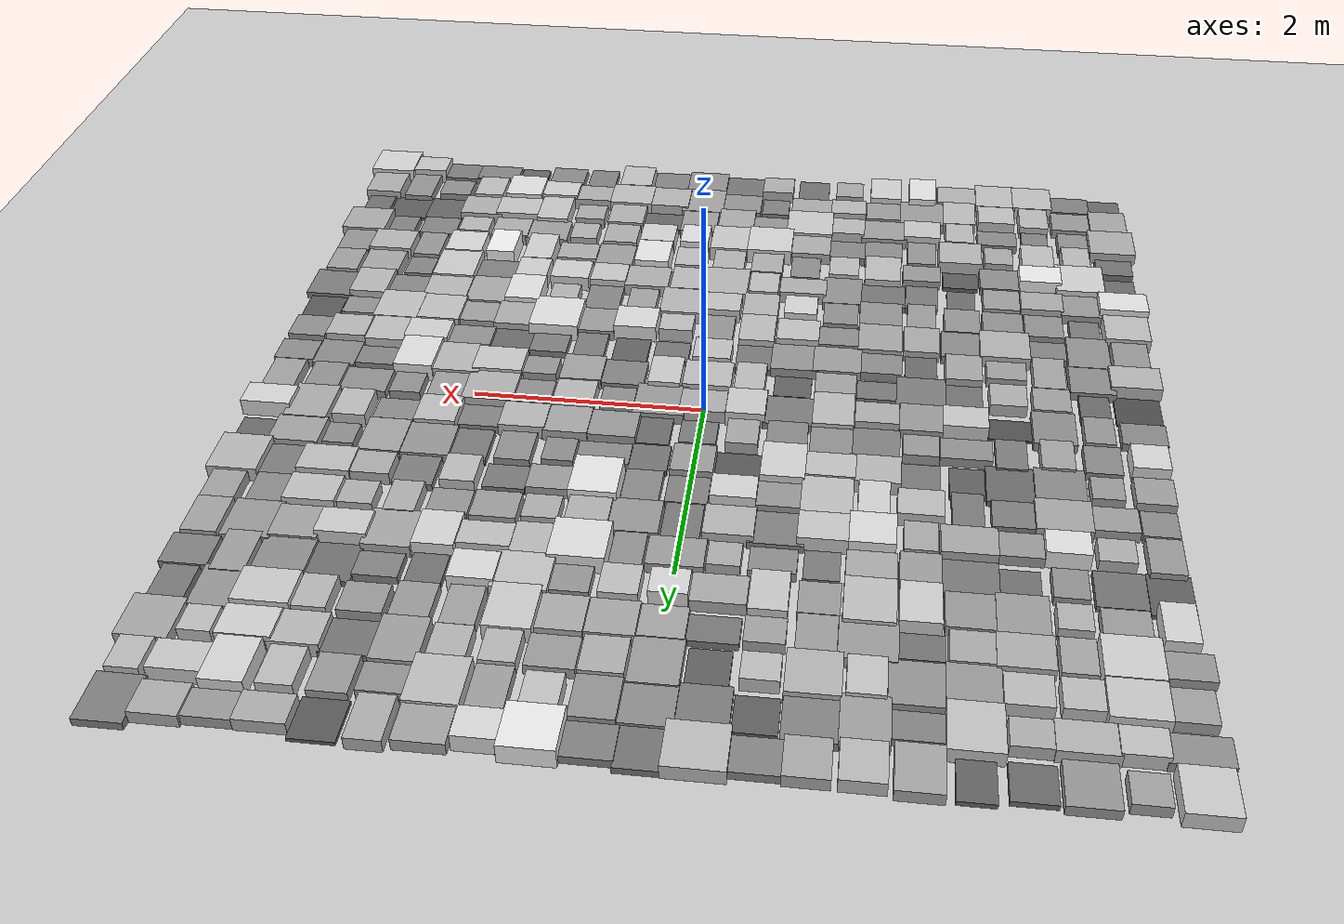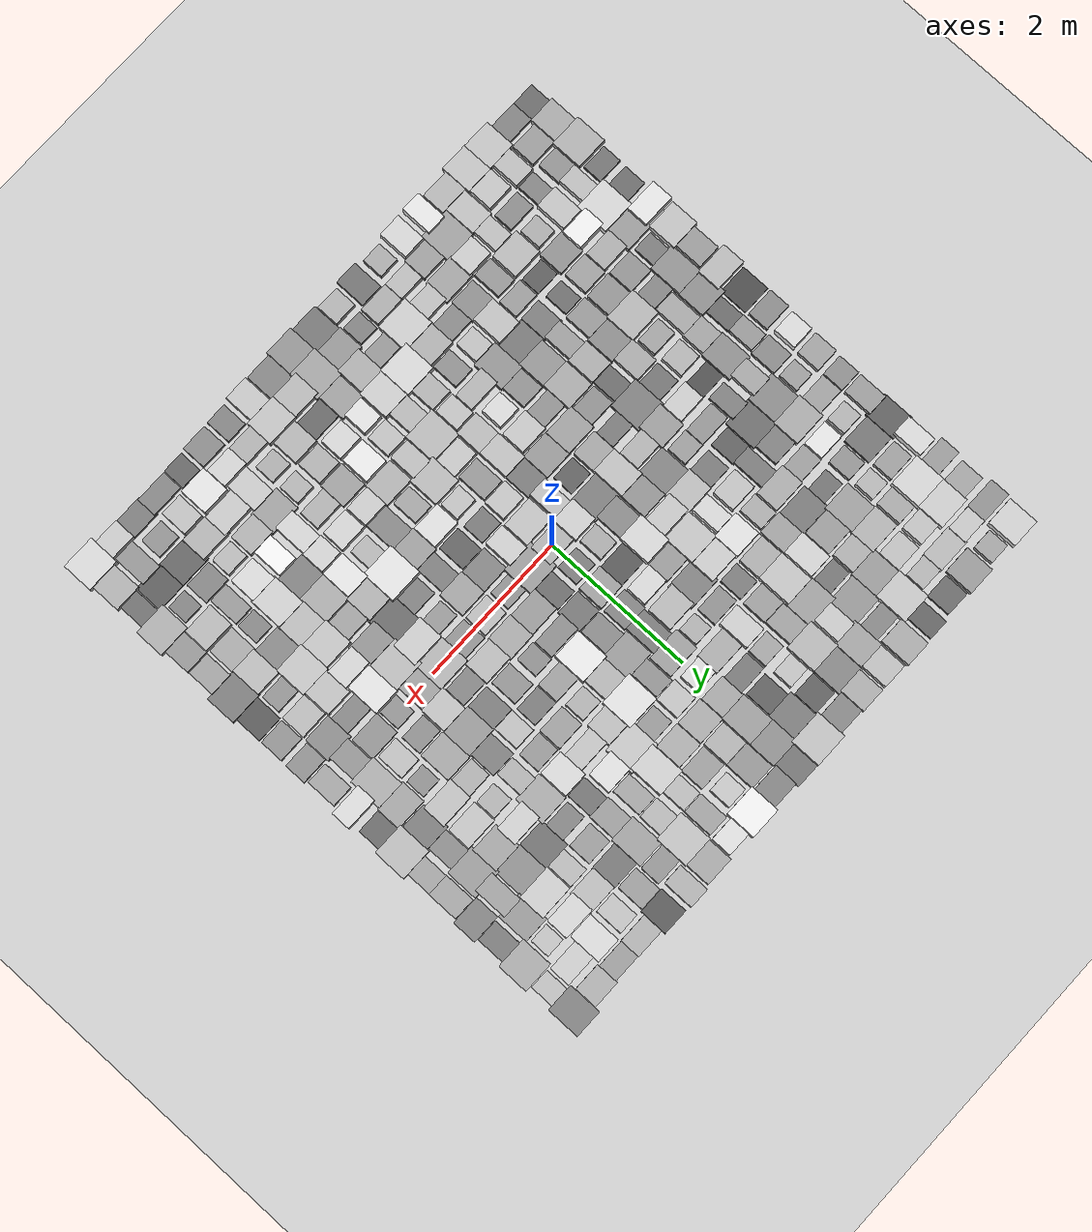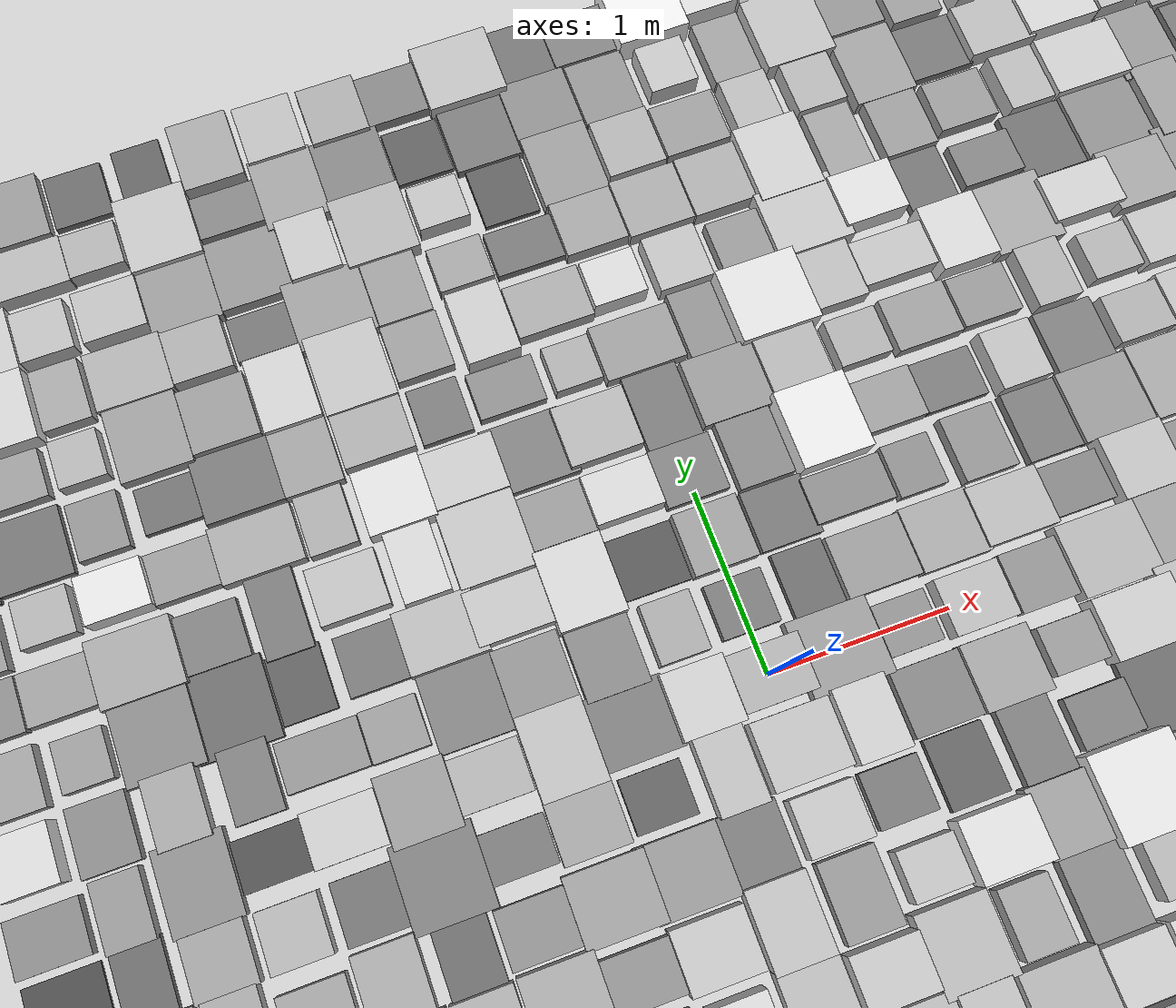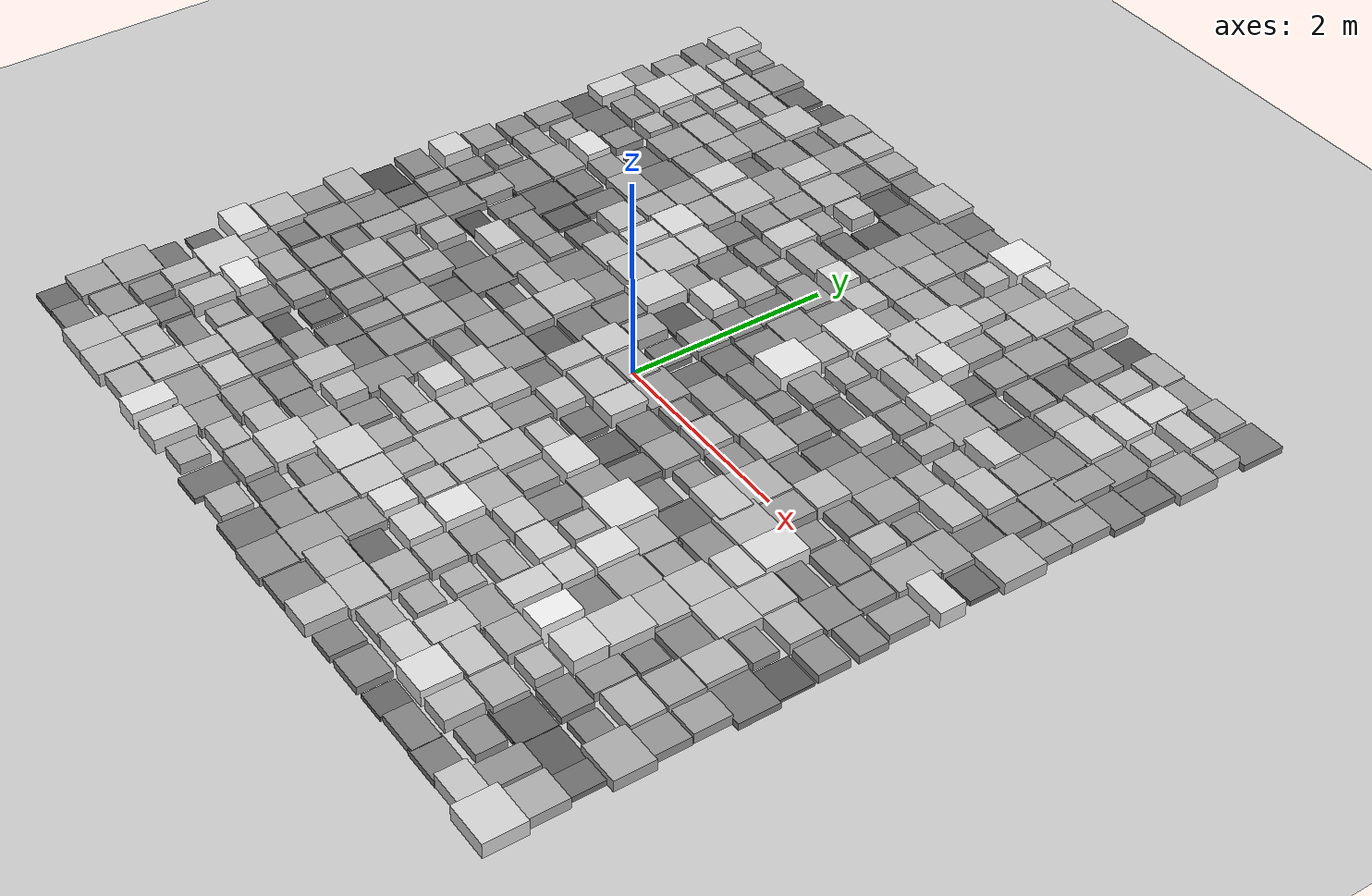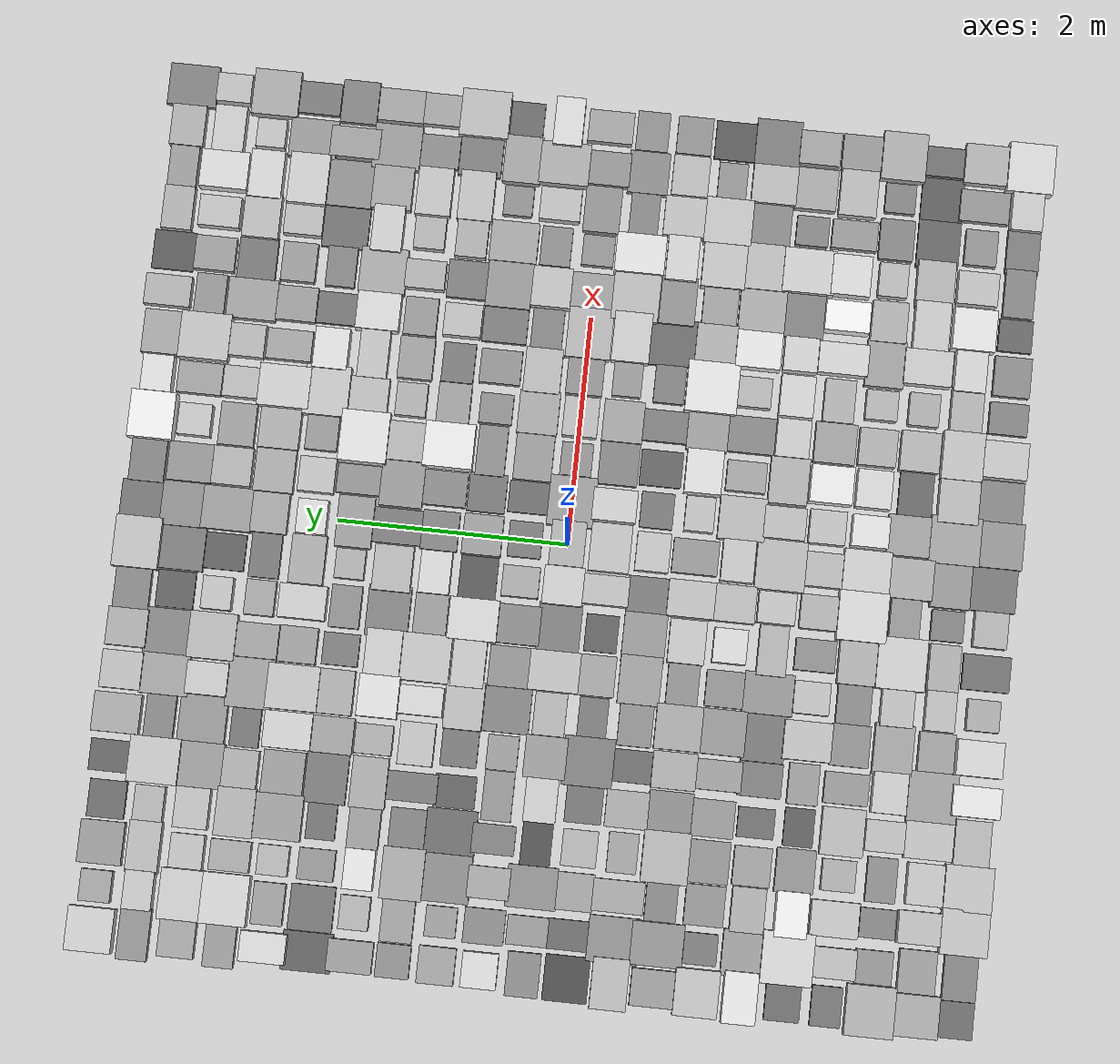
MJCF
<mujoco model="terrain_scene">
  <compiler angle="radian" coordinate="local" inertiafromgeom="true" />
  <option timestep="0.002" gravity="0.0 0.0 -9.81" iterations="50" solver="Newton" />
  <visual>
    <global offwidth="1920" offheight="1080" />
    <quality shadowsize="4096" />
    <headlight ambient="0.4 0.4 0.4" diffuse="0.6 0.6 0.6" />
  </visual>
  <asset>
    <texture name="grid_texture" type="2d" builtin="checker" rgb1="0.9 0.9 0.9" rgb2="0.7 0.7 0.7" width="512" height="512" />
    <material name="grid_material" texture="grid_texture" texrepeat="10 10" reflectance="0.1" />
  </asset>
  <worldbody>
    <geom name="ground" type="plane" size="8.0 8.0 0.1" pos="0 0 0" rgba="0.8 0.8 0.8 1.0" friction="1.0 0.005 0.0001" />
    <geom name="box_0" type="box" size="0.1566 0.1455 0.0247" pos="-3.7000 -3.7000 0.0247" rgba="0.419 0.419 0.419 1.000" friction="1.0 0.005 0.0001" />
    <geom name="box_1" type="box" size="0.1797 0.2169 0.0535" pos="-3.7000 -3.3300 0.0535" rgba="0.654 0.654 0.654 1.000" friction="1.0 0.005 0.0001" />
    <geom name="box_2" type="box" size="0.2166 0.2100 0.0574" pos="-3.7000 -2.9600 0.0574" rgba="0.685 0.685 0.685 1.000" friction="1.0 0.005 0.0001" />
    <geom name="box_3" type="box" size="0.1715 0.1297 0.0284" pos="-3.7000 -2.5900 0.0284" rgba="0.450 0.450 0.450 1.000" friction="1.0 0.005 0.0001" />
    <geom name="box_4" type="box" size="0.1640 0.1508 0.0248" pos="-3.7000 -2.2200 0.0248" rgba="0.421 0.421 0.421 1.000" friction="1.0 0.005 0.0001" />
    <geom name="box_5" type="box" size="0.2203 0.1445 0.0822" pos="-3.7000 -1.8500 0.0822" rgba="0.887 0.887 0.887 1.000" friction="1.0 0.005 0.0001" />
    <geom name="box_6" type="box" size="0.2011 0.1891 0.0647" pos="-3.7000 -1.4800 0.0647" rgba="0.745 0.745 0.745 1.000" friction="1.0 0.005 0.0001" />
    <geom name="box_7" type="box" size="0.1581 0.1896 0.0470" pos="-3.7000 -1.1100 0.0470" rgba="0.601 0.601 0.601 1.000" friction="1.0 0.005 0.0001" />
    <geom name="box_8" type="box" size="0.2188 0.1552 0.0610" pos="-3.7000 -0.7400 0.0610" rgba="0.714 0.714 0.714 1.000" friction="1.0 0.005 0.0001" />
    <geom name="box_9" type="box" size="0.1961 0.1906 0.0100" pos="-3.7000 -0.3700 0.0100" rgba="0.300 0.300 0.300 1.000" friction="1.0 0.005 0.0001" />
    <geom name="box_10" type="box" size="0.1882 0.1409 0.0395" pos="-3.7000 0.0000 0.0395" rgba="0.539 0.539 0.539 1.000" friction="1.0 0.005 0.0001" />
    <geom name="box_11" type="box" size="0.1521 0.1523 0.0764" pos="-3.7000 0.3700 0.0764" rgba="0.840 0.840 0.840 1.000" friction="1.0 0.005 0.0001" />
    <geom name="box_12" type="box" size="0.1582 0.1581 0.0504" pos="-3.7000 0.7400 0.0504" rgba="0.628 0.628 0.628 1.000" friction="1.0 0.005 0.0001" />
    <geom name="box_13" type="box" size="0.1440 0.1443 0.0407" pos="-3.7000 1.1100 0.0407" rgba="0.550 0.550 0.550 1.000" friction="1.0 0.005 0.0001" />
    <geom name="box_14" type="box" size="0.1379 0.1939 0.0477" pos="-3.7000 1.4800 0.0477" rgba="0.606 0.606 0.606 1.000" friction="1.0 0.005 0.0001" />
    <geom name="box_15" type="box" size="0.1677 0.2151 0.0196" pos="-3.7000 1.8500 0.0196" rgba="0.378 0.378 0.378 1.000" friction="1.0 0.005 0.0001" />
    <geom name="box_16" type="box" size="0.1293 0.1971 0.0758" pos="-3.7000 2.2200 0.0758" rgba="0.835 0.835 0.835 1.000" friction="1.0 0.005 0.0001" />
    <geom name="box_17" type="box" size="0.2093 0.1307 0.0468" pos="-3.7000 2.5900 0.0468" rgba="0.599 0.599 0.599 1.000" friction="1.0 0.005 0.0001" />
    <geom name="box_18" type="box" size="0.1627 0.1553 0.0515" pos="-3.7000 2.9600 0.0515" rgba="0.637 0.637 0.637 1.000" friction="1.0 0.005 0.0001" />
    <geom name="box_19" type="box" size="0.2246 0.1314 0.0426" pos="-3.7000 3.3300 0.0426" rgba="0.565 0.565 0.565 1.000" friction="1.0 0.005 0.0001" />
    <geom name="box_20" type="box" size="0.1889 0.1985 0.0718" pos="-3.7000 3.7000 0.0718" rgba="0.802 0.802 0.802 1.000" friction="1.0 0.005 0.0001" />
    <geom name="box_21" type="box" size="0.2108 0.1434 0.0355" pos="-3.3300 -3.7000 0.0355" rgba="0.508 0.508 0.508 1.000" friction="1.0 0.005 0.0001" />
    <geom name="box_22" type="box" size="0.1849 0.1604 0.0476" pos="-3.3300 -3.3300 0.0476" rgba="0.605 0.605 0.605 1.000" friction="1.0 0.005 0.0001" />
    <geom name="box_23" type="box" size="0.1436 0.1582 0.0433" pos="-3.3300 -2.9600 0.0433" rgba="0.570 0.570 0.570 1.000" friction="1.0 0.005 0.0001" />
    <geom name="box_24" type="box" size="0.1307 0.2166 0.0629" pos="-3.3300 -2.5900 0.0629" rgba="0.730 0.730 0.730 1.000" friction="1.0 0.005 0.0001" />
    <geom name="box_25" type="box" size="0.2232 0.2214 0.0745" pos="-3.3300 -2.2200 0.0745" rgba="0.824 0.824 0.824 1.000" friction="1.0 0.005 0.0001" />
    <geom name="box_26" type="box" size="0.1965 0.1851 0.0476" pos="-3.3300 -1.8500 0.0476" rgba="0.605 0.605 0.605 1.000" friction="1.0 0.005 0.0001" />
    <geom name="box_27" type="box" size="0.1346 0.1439 0.0324" pos="-3.3300 -1.4800 0.0324" rgba="0.482 0.482 0.482 1.000" friction="1.0 0.005 0.0001" />
    <geom name="box_28" type="box" size="0.1854 0.2237 0.0432" pos="-3.3300 -1.1100 0.0432" rgba="0.570 0.570 0.570 1.000" friction="1.0 0.005 0.0001" />
    <geom name="box_29" type="box" size="0.1961 0.2235 0.0415" pos="-3.3300 -0.7400 0.0415" rgba="0.556 0.556 0.556 1.000" friction="1.0 0.005 0.0001" />
    <geom name="box_30" type="box" size="0.1290 0.2117 0.0244" pos="-3.3300 -0.3700 0.0244" rgba="0.417 0.417 0.417 1.000" friction="1.0 0.005 0.0001" />
    <geom name="box_31" type="box" size="0.1254 0.1757 0.0459" pos="-3.3300 0.0000 0.0459" rgba="0.592 0.592 0.592 1.000" friction="1.0 0.005 0.0001" />
    <geom name="box_32" type="box" size="0.1507 0.1742 0.0393" pos="-3.3300 0.3700 0.0393" rgba="0.538 0.538 0.538 1.000" friction="1.0 0.005 0.0001" />
    <geom name="box_33" type="box" size="0.1308 0.1331 0.0478" pos="-3.3300 0.7400 0.0478" rgba="0.607 0.607 0.607 1.000" friction="1.0 0.005 0.0001" />
    <geom name="box_34" type="box" size="0.2114 0.1393 0.0496" pos="-3.3300 1.1100 0.0496" rgba="0.621 0.621 0.621 1.000" friction="1.0 0.005 0.0001" />
    <geom name="box_35" type="box" size="0.1445 0.1277 0.0581" pos="-3.3300 1.4800 0.0581" rgba="0.691 0.691 0.691 1.000" friction="1.0 0.005 0.0001" />
    <geom name="box_36" type="box" size="0.1950 0.1898 0.0291" pos="-3.3300 1.8500 0.0291" rgba="0.455 0.455 0.455 1.000" friction="1.0 0.005 0.0001" />
    <geom name="box_37" type="box" size="0.1805 0.1344 0.0485" pos="-3.3300 2.2200 0.0485" rgba="0.613 0.613 0.613 1.000" friction="1.0 0.005 0.0001" />
    <geom name="box_38" type="box" size="0.2182 0.2012 0.0740" pos="-3.3300 2.5900 0.0740" rgba="0.820 0.820 0.820 1.000" friction="1.0 0.005 0.0001" />
    <geom name="box_39" type="box" size="0.2167 0.1899 0.0701" pos="-3.3300 2.9600 0.0701" rgba="0.788 0.788 0.788 1.000" friction="1.0 0.005 0.0001" />
    <geom name="box_40" type="box" size="0.1667 0.1254 0.0669" pos="-3.3300 3.3300 0.0669" rgba="0.763 0.763 0.763 1.000" friction="1.0 0.005 0.0001" />
    <geom name="box_41" type="box" size="0.1359 0.1345 0.0513" pos="-3.3300 3.7000 0.0513" rgba="0.635 0.635 0.635 1.000" friction="1.0 0.005 0.0001" />
    <geom name="box_42" type="box" size="0.1951 0.2041 0.0656" pos="-2.9600 -3.7000 0.0656" rgba="0.752 0.752 0.752 1.000" friction="1.0 0.005 0.0001" />
    <geom name="box_43" type="box" size="0.1396 0.1998 0.0628" pos="-2.9600 -3.3300 0.0628" rgba="0.729 0.729 0.729 1.000" friction="1.0 0.005 0.0001" />
    <geom name="box_44" type="box" size="0.1263 0.1531 0.0362" pos="-2.9600 -2.9600 0.0362" rgba="0.513 0.513 0.513 1.000" friction="1.0 0.005 0.0001" />
    <geom name="box_45" type="box" size="0.1524 0.2062 0.0657" pos="-2.9600 -2.5900 0.0657" rgba="0.753 0.753 0.753 1.000" friction="1.0 0.005 0.0001" />
    <geom name="box_46" type="box" size="0.1946 0.1389 0.0868" pos="-2.9600 -2.2200 0.0868" rgba="0.924 0.924 0.924 1.000" friction="1.0 0.005 0.0001" />
    <geom name="box_47" type="box" size="0.1927 0.1445 0.0560" pos="-2.9600 -1.8500 0.0560" rgba="0.673 0.673 0.673 1.000" friction="1.0 0.005 0.0001" />
    <geom name="box_48" type="box" size="0.1734 0.1689 0.0432" pos="-2.9600 -1.4800 0.0432" rgba="0.570 0.570 0.570 1.000" friction="1.0 0.005 0.0001" />
    <geom name="box_49" type="box" size="0.1768 0.1350 0.0372" pos="-2.9600 -1.1100 0.0372" rgba="0.521 0.521 0.521 1.000" friction="1.0 0.005 0.0001" />
    <geom name="box_50" type="box" size="0.1383 0.2204 0.0528" pos="-2.9600 -0.7400 0.0528" rgba="0.648 0.648 0.648 1.000" friction="1.0 0.005 0.0001" />
    <geom name="box_51" type="box" size="0.1605 0.1572 0.0507" pos="-2.9600 -0.3700 0.0507" rgba="0.630 0.630 0.630 1.000" friction="1.0 0.005 0.0001" />
    <geom name="box_52" type="box" size="0.1813 0.2169 0.0415" pos="-2.9600 0.0000 0.0415" rgba="0.556 0.556 0.556 1.000" friction="1.0 0.005 0.0001" />
    <geom name="box_53" type="box" size="0.1365 0.1806 0.0526" pos="-2.9600 0.3700 0.0526" rgba="0.646 0.646 0.646 1.000" friction="1.0 0.005 0.0001" />
    <geom name="box_54" type="box" size="0.2052 0.2129 0.0399" pos="-2.9600 0.7400 0.0399" rgba="0.543 0.543 0.543 1.000" friction="1.0 0.005 0.0001" />
    <geom name="box_55" type="box" size="0.2221 0.1803 0.0538" pos="-2.9600 1.1100 0.0538" rgba="0.656 0.656 0.656 1.000" friction="1.0 0.005 0.0001" />
    <geom name="box_56" type="box" size="0.1739 0.1287 0.0822" pos="-2.9600 1.4800 0.0822" rgba="0.886 0.886 0.886 1.000" friction="1.0 0.005 0.0001" />
    <geom name="box_57" type="box" size="0.1351 0.1559 0.0437" pos="-2.9600 1.8500 0.0437" rgba="0.573 0.573 0.573 1.000" friction="1.0 0.005 0.0001" />
    <geom name="box_58" type="box" size="0.1293 0.1329 0.0594" pos="-2.9600 2.2200 0.0594" rgba="0.702 0.702 0.702 1.000" friction="1.0 0.005 0.0001" />
    <geom name="box_59" type="box" size="0.1322 0.1727 0.0535" pos="-2.9600 2.5900 0.0535" rgba="0.653 0.653 0.653 1.000" friction="1.0 0.005 0.0001" />
    <geom name="box_60" type="box" size="0.1478 0.1439 0.0643" pos="-2.9600 2.9600 0.0643" rgba="0.741 0.741 0.741 1.000" friction="1.0 0.005 0.0001" />
    <geom name="box_61" type="box" size="0.2202 0.1390 0.0608" pos="-2.9600 3.3300 0.0608" rgba="0.713 0.713 0.713 1.000" friction="1.0 0.005 0.0001" />
    <geom name="box_62" type="box" size="0.1845 0.1892 0.0465" pos="-2.9600 3.7000 0.0465" rgba="0.596 0.596 0.596 1.000" friction="1.0 0.005 0.0001" />
    <geom name="box_63" type="box" size="0.1954 0.2070 0.0656" pos="-2.5900 -3.7000 0.0656" rgba="0.751 0.751 0.751 1.000" friction="1.0 0.005 0.0001" />
    <geom name="box_64" type="box" size="0.1783 0.1574 0.0659" pos="-2.5900 -3.3300 0.0659" rgba="0.754 0.754 0.754 1.000" friction="1.0 0.005 0.0001" />
    <geom name="box_65" type="box" size="0.1915 0.1284 0.0396" pos="-2.5900 -2.9600 0.0396" rgba="0.541 0.541 0.541 1.000" friction="1.0 0.005 0.0001" />
    <geom name="box_66" type="box" size="0.1344 0.1441 0.0555" pos="-2.5900 -2.5900 0.0555" rgba="0.669 0.669 0.669 1.000" friction="1.0 0.005 0.0001" />
    <geom name="box_67" type="box" size="0.1878 0.1671 0.0425" pos="-2.5900 -2.2200 0.0425" rgba="0.564 0.564 0.564 1.000" friction="1.0 0.005 0.0001" />
    <geom name="box_68" type="box" size="0.1683 0.1603 0.0496" pos="-2.5900 -1.8500 0.0496" rgba="0.622 0.622 0.622 1.000" friction="1.0 0.005 0.0001" />
    <geom name="box_69" type="box" size="0.1829 0.1742 0.0434" pos="-2.5900 -1.4800 0.0434" rgba="0.571 0.571 0.571 1.000" friction="1.0 0.005 0.0001" />
    <geom name="box_70" type="box" size="0.2216 0.2006 0.0594" pos="-2.5900 -1.1100 0.0594" rgba="0.702 0.702 0.702 1.000" friction="1.0 0.005 0.0001" />
    <geom name="box_71" type="box" size="0.1729 0.1276 0.0507" pos="-2.5900 -0.7400 0.0507" rgba="0.630 0.630 0.630 1.000" friction="1.0 0.005 0.0001" />
    <geom name="box_72" type="box" size="0.1569 0.1506 0.0585" pos="-2.5900 -0.3700 0.0585" rgba="0.694 0.694 0.694 1.000" friction="1.0 0.005 0.0001" />
    <geom name="box_73" type="box" size="0.1969 0.1297 0.0121" pos="-2.5900 0.0000 0.0121" rgba="0.317 0.317 0.317 1.000" friction="1.0 0.005 0.0001" />
    <geom name="box_74" type="box" size="0.1276 0.1850 0.0344" pos="-2.5900 0.3700 0.0344" rgba="0.498 0.498 0.498 1.000" friction="1.0 0.005 0.0001" />
    <geom name="box_75" type="box" size="0.2183 0.2187 0.0257" pos="-2.5900 0.7400 0.0257" rgba="0.428 0.428 0.428 1.000" friction="1.0 0.005 0.0001" />
    <geom name="box_76" type="box" size="0.1867 0.1542 0.0350" pos="-2.5900 1.1100 0.0350" rgba="0.503 0.503 0.503 1.000" friction="1.0 0.005 0.0001" />
    <geom name="box_77" type="box" size="0.1987 0.1352 0.0482" pos="-2.5900 1.4800 0.0482" rgba="0.610 0.610 0.610 1.000" friction="1.0 0.005 0.0001" />
    <geom name="box_78" type="box" size="0.1561 0.1262 0.0280" pos="-2.5900 1.8500 0.0280" rgba="0.446 0.446 0.446 1.000" friction="1.0 0.005 0.0001" />
    <geom name="box_79" type="box" size="0.1958 0.2051 0.0490" pos="-2.5900 2.2200 0.0490" rgba="0.617 0.617 0.617 1.000" friction="1.0 0.005 0.0001" />
    <geom name="box_80" type="box" size="0.2097 0.1657 0.0576" pos="-2.5900 2.5900 0.0576" rgba="0.687 0.687 0.687 1.000" friction="1.0 0.005 0.0001" />
    <geom name="box_81" type="box" size="0.1756 0.1473 0.0639" pos="-2.5900 2.9600 0.0639" rgba="0.738 0.738 0.738 1.000" friction="1.0 0.005 0.0001" />
    <geom name="box_82" type="box" size="0.1525 0.1276 0.0582" pos="-2.5900 3.3300 0.0582" rgba="0.692 0.692 0.692 1.000" friction="1.0 0.005 0.0001" />
    <geom name="box_83" type="box" size="0.1617 0.1601 0.0245" pos="-2.5900 3.7000 0.0245" rgba="0.418 0.418 0.418 1.000" friction="1.0 0.005 0.0001" />
    <geom name="box_84" type="box" size="0.2133 0.1542 0.0595" pos="-2.2200 -3.7000 0.0595" rgba="0.702 0.702 0.702 1.000" friction="1.0 0.005 0.0001" />
    <geom name="box_85" type="box" size="0.1590 0.2072 0.0641" pos="-2.2200 -3.3300 0.0641" rgba="0.740 0.740 0.740 1.000" friction="1.0 0.005 0.0001" />
    <geom name="box_86" type="box" size="0.1354 0.1753 0.0627" pos="-2.2200 -2.9600 0.0627" rgba="0.728 0.728 0.728 1.000" friction="1.0 0.005 0.0001" />
    <geom name="box_87" type="box" size="0.2046 0.1840 0.0611" pos="-2.2200 -2.5900 0.0611" rgba="0.715 0.715 0.715 1.000" friction="1.0 0.005 0.0001" />
    <geom name="box_88" type="box" size="0.1643 0.1283 0.0183" pos="-2.2200 -2.2200 0.0183" rgba="0.367 0.367 0.367 1.000" friction="1.0 0.005 0.0001" />
    <geom name="box_89" type="box" size="0.1289 0.1579 0.0259" pos="-2.2200 -1.8500 0.0259" rgba="0.430 0.430 0.430 1.000" friction="1.0 0.005 0.0001" />
    <geom name="box_90" type="box" size="0.1606 0.1811 0.0457" pos="-2.2200 -1.4800 0.0457" rgba="0.590 0.590 0.590 1.000" friction="1.0 0.005 0.0001" />
    <geom name="box_91" type="box" size="0.1928 0.1917 0.0405" pos="-2.2200 -1.1100 0.0405" rgba="0.548 0.548 0.548 1.000" friction="1.0 0.005 0.0001" />
    <geom name="box_92" type="box" size="0.1596 0.1835 0.0540" pos="-2.2200 -0.7400 0.0540" rgba="0.658 0.658 0.658 1.000" friction="1.0 0.005 0.0001" />
    <geom name="box_93" type="box" size="0.1565 0.1580 0.0286" pos="-2.2200 -0.3700 0.0286" rgba="0.451 0.451 0.451 1.000" friction="1.0 0.005 0.0001" />
    <geom name="box_94" type="box" size="0.1897 0.1385 0.0701" pos="-2.2200 0.0000 0.0701" rgba="0.788 0.788 0.788 1.000" friction="1.0 0.005 0.0001" />
    <geom name="box_95" type="box" size="0.2143 0.1286 0.0439" pos="-2.2200 0.3700 0.0439" rgba="0.576 0.576 0.576 1.000" friction="1.0 0.005 0.0001" />
    <geom name="box_96" type="box" size="0.1413 0.1757 0.0198" pos="-2.2200 0.7400 0.0198" rgba="0.380 0.380 0.380 1.000" friction="1.0 0.005 0.0001" />
    <geom name="box_97" type="box" size="0.1260 0.2165 0.0323" pos="-2.2200 1.1100 0.0323" rgba="0.481 0.481 0.481 1.000" friction="1.0 0.005 0.0001" />
    <geom name="box_98" type="box" size="0.2204 0.1537 0.0548" pos="-2.2200 1.4800 0.0548" rgba="0.664 0.664 0.664 1.000" friction="1.0 0.005 0.0001" />
    <geom name="box_99" type="box" size="0.2172 0.1807 0.0318" pos="-2.2200 1.8500 0.0318" rgba="0.477 0.477 0.477 1.000" friction="1.0 0.005 0.0001" />
    <geom name="box_100" type="box" size="0.1935 0.1799 0.0476" pos="-2.2200 2.2200 0.0476" rgba="0.606 0.606 0.606 1.000" friction="1.0 0.005 0.0001" />
    <geom name="box_101" type="box" size="0.1689 0.1519 0.0562" pos="-2.2200 2.5900 0.0562" rgba="0.675 0.675 0.675 1.000" friction="1.0 0.005 0.0001" />
    <geom name="box_102" type="box" size="0.1949 0.2224 0.0471" pos="-2.2200 2.9600 0.0471" rgba="0.602 0.602 0.602 1.000" friction="1.0 0.005 0.0001" />
    <geom name="box_103" type="box" size="0.1990 0.2177 0.0672" pos="-2.2200 3.3300 0.0672" rgba="0.765 0.765 0.765 1.000" friction="1.0 0.005 0.0001" />
    <geom name="box_104" type="box" size="0.1360 0.1942 0.0212" pos="-2.2200 3.7000 0.0212" rgba="0.391 0.391 0.391 1.000" friction="1.0 0.005 0.0001" />
    <geom name="box_105" type="box" size="0.1319 0.2084 0.0828" pos="-1.8500 -3.7000 0.0828" rgba="0.892 0.892 0.892 1.000" friction="1.0 0.005 0.0001" />
    <geom name="box_106" type="box" size="0.2157 0.2128 0.0494" pos="-1.8500 -3.3300 0.0494" rgba="0.620 0.620 0.620 1.000" friction="1.0 0.005 0.0001" />
    <geom name="box_107" type="box" size="0.1766 0.1502 0.0693" pos="-1.8500 -2.9600 0.0693" rgba="0.781 0.781 0.781 1.000" friction="1.0 0.005 0.0001" />
    <geom name="box_108" type="box" size="0.1351 0.1909 0.0455" pos="-1.8500 -2.5900 0.0455" rgba="0.588 0.588 0.588 1.000" friction="1.0 0.005 0.0001" />
    <geom name="box_109" type="box" size="0.1761 0.1304 0.0476" pos="-1.8500 -2.2200 0.0476" rgba="0.605 0.605 0.605 1.000" friction="1.0 0.005 0.0001" />
    <geom name="box_110" type="box" size="0.1482 0.1870 0.0332" pos="-1.8500 -1.8500 0.0332" rgba="0.488 0.488 0.488 1.000" friction="1.0 0.005 0.0001" />
    <geom name="box_111" type="box" size="0.1307 0.2100 0.0487" pos="-1.8500 -1.4800 0.0487" rgba="0.614 0.614 0.614 1.000" friction="1.0 0.005 0.0001" />
    <geom name="box_112" type="box" size="0.1592 0.1909 0.0553" pos="-1.8500 -1.1100 0.0553" rgba="0.668 0.668 0.668 1.000" friction="1.0 0.005 0.0001" />
    <geom name="box_113" type="box" size="0.1404 0.1779 0.0251" pos="-1.8500 -0.7400 0.0251" rgba="0.422 0.422 0.422 1.000" friction="1.0 0.005 0.0001" />
    <geom name="box_114" type="box" size="0.2128 0.2174 0.0342" pos="-1.8500 -0.3700 0.0342" rgba="0.496 0.496 0.496 1.000" friction="1.0 0.005 0.0001" />
    <geom name="box_115" type="box" size="0.1813 0.1808 0.0479" pos="-1.8500 0.0000 0.0479" rgba="0.608 0.608 0.608 1.000" friction="1.0 0.005 0.0001" />
    <geom name="box_116" type="box" size="0.1498 0.1326 0.0478" pos="-1.8500 0.3700 0.0478" rgba="0.607 0.607 0.607 1.000" friction="1.0 0.005 0.0001" />
    <geom name="box_117" type="box" size="0.1579 0.1572 0.0313" pos="-1.8500 0.7400 0.0313" rgba="0.473 0.473 0.473 1.000" friction="1.0 0.005 0.0001" />
    <geom name="box_118" type="box" size="0.1846 0.1514 0.0649" pos="-1.8500 1.1100 0.0649" rgba="0.746 0.746 0.746 1.000" friction="1.0 0.005 0.0001" />
    <geom name="box_119" type="box" size="0.1290 0.1614 0.0553" pos="-1.8500 1.4800 0.0553" rgba="0.668 0.668 0.668 1.000" friction="1.0 0.005 0.0001" />
    <geom name="box_120" type="box" size="0.1587 0.1929 0.0503" pos="-1.8500 1.8500 0.0503" rgba="0.628 0.628 0.628 1.000" friction="1.0 0.005 0.0001" />
    <geom name="box_121" type="box" size="0.1578 0.2072 0.0727" pos="-1.8500 2.2200 0.0727" rgba="0.809 0.809 0.809 1.000" friction="1.0 0.005 0.0001" />
    <geom name="box_122" type="box" size="0.1809 0.1251 0.0295" pos="-1.8500 2.5900 0.0295" rgba="0.458 0.458 0.458 1.000" friction="1.0 0.005 0.0001" />
    <geom name="box_123" type="box" size="0.2241 0.2032 0.0451" pos="-1.8500 2.9600 0.0451" rgba="0.585 0.585 0.585 1.000" friction="1.0 0.005 0.0001" />
    <geom name="box_124" type="box" size="0.2152 0.1270 0.0373" pos="-1.8500 3.3300 0.0373" rgba="0.522 0.522 0.522 1.000" friction="1.0 0.005 0.0001" />
    <geom name="box_125" type="box" size="0.1701 0.2040 0.0539" pos="-1.8500 3.7000 0.0539" rgba="0.657 0.657 0.657 1.000" friction="1.0 0.005 0.0001" />
    <geom name="box_126" type="box" size="0.1538 0.2001 0.0743" pos="-1.4800 -3.7000 0.0743" rgba="0.823 0.823 0.823 1.000" friction="1.0 0.005 0.0001" />
    <geom name="box_127" type="box" size="0.1870 0.1551 0.0492" pos="-1.4800 -3.3300 0.0492" rgba="0.619 0.619 0.619 1.000" friction="1.0 0.005 0.0001" />
    <geom name="box_128" type="box" size="0.2217 0.1689 0.0511" pos="-1.4800 -2.9600 0.0511" rgba="0.634 0.634 0.634 1.000" friction="1.0 0.005 0.0001" />
    <geom name="box_129" type="box" size="0.1802 0.1660 0.0416" pos="-1.4800 -2.5900 0.0416" rgba="0.557 0.557 0.557 1.000" friction="1.0 0.005 0.0001" />
    <geom name="box_130" type="box" size="0.1682 0.2077 0.0644" pos="-1.4800 -2.2200 0.0644" rgba="0.742 0.742 0.742 1.000" friction="1.0 0.005 0.0001" />
    <geom name="box_131" type="box" size="0.2182 0.1814 0.0308" pos="-1.4800 -1.8500 0.0308" rgba="0.469 0.469 0.469 1.000" friction="1.0 0.005 0.0001" />
    <geom name="box_132" type="box" size="0.1955 0.2088 0.0447" pos="-1.4800 -1.4800 0.0447" rgba="0.582 0.582 0.582 1.000" friction="1.0 0.005 0.0001" />
    <geom name="box_133" type="box" size="0.1950 0.2000 0.0541" pos="-1.4800 -1.1100 0.0541" rgba="0.658 0.658 0.658 1.000" friction="1.0 0.005 0.0001" />
    <geom name="box_134" type="box" size="0.1996 0.1459 0.0418" pos="-1.4800 -0.7400 0.0418" rgba="0.558 0.558 0.558 1.000" friction="1.0 0.005 0.0001" />
    <geom name="box_135" type="box" size="0.1838 0.1252 0.0317" pos="-1.4800 -0.3700 0.0317" rgba="0.476 0.476 0.476 1.000" friction="1.0 0.005 0.0001" />
    <geom name="box_136" type="box" size="0.1860 0.1379 0.0580" pos="-1.4800 0.0000 0.0580" rgba="0.690 0.690 0.690 1.000" friction="1.0 0.005 0.0001" />
    <geom name="box_137" type="box" size="0.1967 0.2008 0.0358" pos="-1.4800 0.3700 0.0358" rgba="0.510 0.510 0.510 1.000" friction="1.0 0.005 0.0001" />
    <geom name="box_138" type="box" size="0.2104 0.1664 0.0622" pos="-1.4800 0.7400 0.0622" rgba="0.724 0.724 0.724 1.000" friction="1.0 0.005 0.0001" />
    <geom name="box_139" type="box" size="0.1251 0.1895 0.0749" pos="-1.4800 1.1100 0.0749" rgba="0.827 0.827 0.827 1.000" friction="1.0 0.005 0.0001" />
    <geom name="box_140" type="box" size="0.1817 0.1747 0.0796" pos="-1.4800 1.4800 0.0796" rgba="0.866 0.866 0.866 1.000" friction="1.0 0.005 0.0001" />
    <geom name="box_141" type="box" size="0.1931 0.1528 0.0558" pos="-1.4800 1.8500 0.0558" rgba="0.672 0.672 0.672 1.000" friction="1.0 0.005 0.0001" />
    <geom name="box_142" type="box" size="0.1957 0.2238 0.0661" pos="-1.4800 2.2200 0.0661" rgba="0.756 0.756 0.756 1.000" friction="1.0 0.005 0.0001" />
    <geom name="box_143" type="box" size="0.2169 0.2005 0.0494" pos="-1.4800 2.5900 0.0494" rgba="0.620 0.620 0.620 1.000" friction="1.0 0.005 0.0001" />
    <geom name="box_144" type="box" size="0.1422 0.1793 0.0685" pos="-1.4800 2.9600 0.0685" rgba="0.776 0.776 0.776 1.000" friction="1.0 0.005 0.0001" />
    <geom name="box_145" type="box" size="0.1771 0.2118 0.0511" pos="-1.4800 3.3300 0.0511" rgba="0.634 0.634 0.634 1.000" friction="1.0 0.005 0.0001" />
    <geom name="box_146" type="box" size="0.1631 0.1756 0.0634" pos="-1.4800 3.7000 0.0634" rgba="0.734 0.734 0.734 1.000" friction="1.0 0.005 0.0001" />
    <geom name="box_147" type="box" size="0.1359 0.1404 0.0548" pos="-1.1100 -3.7000 0.0548" rgba="0.664 0.664 0.664 1.000" friction="1.0 0.005 0.0001" />
    <geom name="box_148" type="box" size="0.1734 0.1299 0.0625" pos="-1.1100 -3.3300 0.0625" rgba="0.727 0.727 0.727 1.000" friction="1.0 0.005 0.0001" />
    <geom name="box_149" type="box" size="0.1723 0.1414 0.0632" pos="-1.1100 -2.9600 0.0632" rgba="0.732 0.732 0.732 1.000" friction="1.0 0.005 0.0001" />
    <geom name="box_150" type="box" size="0.2045 0.1478 0.0387" pos="-1.1100 -2.5900 0.0387" rgba="0.534 0.534 0.534 1.000" friction="1.0 0.005 0.0001" />
    <geom name="box_151" type="box" size="0.1404 0.1554 0.0641" pos="-1.1100 -2.2200 0.0641" rgba="0.740 0.740 0.740 1.000" friction="1.0 0.005 0.0001" />
    <geom name="box_152" type="box" size="0.1794 0.2136 0.0443" pos="-1.1100 -1.8500 0.0443" rgba="0.578 0.578 0.578 1.000" friction="1.0 0.005 0.0001" />
    <geom name="box_153" type="box" size="0.1580 0.1721 0.0427" pos="-1.1100 -1.4800 0.0427" rgba="0.566 0.566 0.566 1.000" friction="1.0 0.005 0.0001" />
    <geom name="box_154" type="box" size="0.2248 0.1364 0.0424" pos="-1.1100 -1.1100 0.0424" rgba="0.563 0.563 0.563 1.000" friction="1.0 0.005 0.0001" />
    <geom name="box_155" type="box" size="0.2114 0.1803 0.0496" pos="-1.1100 -0.7400 0.0496" rgba="0.622 0.622 0.622 1.000" friction="1.0 0.005 0.0001" />
    <geom name="box_156" type="box" size="0.1769 0.1542 0.0518" pos="-1.1100 -0.3700 0.0518" rgba="0.640 0.640 0.640 1.000" friction="1.0 0.005 0.0001" />
    <geom name="box_157" type="box" size="0.1748 0.2176 0.0641" pos="-1.1100 0.0000 0.0641" rgba="0.740 0.740 0.740 1.000" friction="1.0 0.005 0.0001" />
    <geom name="box_158" type="box" size="0.1764 0.1961 0.0435" pos="-1.1100 0.3700 0.0435" rgba="0.572 0.572 0.572 1.000" friction="1.0 0.005 0.0001" />
    <geom name="box_159" type="box" size="0.2155 0.1434 0.0671" pos="-1.1100 0.7400 0.0671" rgba="0.764 0.764 0.764 1.000" friction="1.0 0.005 0.0001" />
    <geom name="box_160" type="box" size="0.2062 0.2111 0.0661" pos="-1.1100 1.1100 0.0661" rgba="0.756 0.756 0.756 1.000" friction="1.0 0.005 0.0001" />
    <geom name="box_161" type="box" size="0.2087 0.1557 0.0696" pos="-1.1100 1.4800 0.0696" rgba="0.785 0.785 0.785 1.000" friction="1.0 0.005 0.0001" />
    <geom name="box_162" type="box" size="0.1390 0.1557 0.0328" pos="-1.1100 1.8500 0.0328" rgba="0.485 0.485 0.485 1.000" friction="1.0 0.005 0.0001" />
    <geom name="box_163" type="box" size="0.1572 0.1637 0.0487" pos="-1.1100 2.2200 0.0487" rgba="0.614 0.614 0.614 1.000" friction="1.0 0.005 0.0001" />
    <geom name="box_164" type="box" size="0.1507 0.1995 0.0498" pos="-1.1100 2.5900 0.0498" rgba="0.623 0.623 0.623 1.000" friction="1.0 0.005 0.0001" />
    <geom name="box_165" type="box" size="0.2016 0.2042 0.0603" pos="-1.1100 2.9600 0.0603" rgba="0.709 0.709 0.709 1.000" friction="1.0 0.005 0.0001" />
    <geom name="box_166" type="box" size="0.1972 0.2165 0.0373" pos="-1.1100 3.3300 0.0373" rgba="0.522 0.522 0.522 1.000" friction="1.0 0.005 0.0001" />
    <geom name="box_167" type="box" size="0.1640 0.1734 0.0553" pos="-1.1100 3.7000 0.0553" rgba="0.668 0.668 0.668 1.000" friction="1.0 0.005 0.0001" />
    <geom name="box_168" type="box" size="0.1543 0.2054 0.0280" pos="-0.7400 -3.7000 0.0280" rgba="0.446 0.446 0.446 1.000" friction="1.0 0.005 0.0001" />
    <geom name="box_169" type="box" size="0.2056 0.1337 0.0559" pos="-0.7400 -3.3300 0.0559" rgba="0.673 0.673 0.673 1.000" friction="1.0 0.005 0.0001" />
    <geom name="box_170" type="box" size="0.2248 0.2119 0.0708" pos="-0.7400 -2.9600 0.0708" rgba="0.794 0.794 0.794 1.000" friction="1.0 0.005 0.0001" />
    <geom name="box_171" type="box" size="0.2201 0.1688 0.0570" pos="-0.7400 -2.5900 0.0570" rgba="0.682 0.682 0.682 1.000" friction="1.0 0.005 0.0001" />
    <geom name="box_172" type="box" size="0.1380 0.1751 0.0418" pos="-0.7400 -2.2200 0.0418" rgba="0.558 0.558 0.558 1.000" friction="1.0 0.005 0.0001" />
    <geom name="box_173" type="box" size="0.2186 0.1254 0.0582" pos="-0.7400 -1.8500 0.0582" rgba="0.692 0.692 0.692 1.000" friction="1.0 0.005 0.0001" />
    <geom name="box_174" type="box" size="0.1496 0.1449 0.0763" pos="-0.7400 -1.4800 0.0763" rgba="0.839 0.839 0.839 1.000" friction="1.0 0.005 0.0001" />
    <geom name="box_175" type="box" size="0.1906 0.1578 0.0670" pos="-0.7400 -1.1100 0.0670" rgba="0.763 0.763 0.763 1.000" friction="1.0 0.005 0.0001" />
    <geom name="box_176" type="box" size="0.2140 0.1853 0.0460" pos="-0.7400 -0.7400 0.0460" rgba="0.592 0.592 0.592 1.000" friction="1.0 0.005 0.0001" />
    <geom name="box_177" type="box" size="0.1616 0.1410 0.0202" pos="-0.7400 -0.3700 0.0202" rgba="0.383 0.383 0.383 1.000" friction="1.0 0.005 0.0001" />
    <geom name="box_178" type="box" size="0.2214 0.1872 0.0337" pos="-0.7400 0.0000 0.0337" rgba="0.492 0.492 0.492 1.000" friction="1.0 0.005 0.0001" />
    <geom name="box_179" type="box" size="0.1701 0.2086 0.0392" pos="-0.7400 0.3700 0.0392" rgba="0.537 0.537 0.537 1.000" friction="1.0 0.005 0.0001" />
    <geom name="box_180" type="box" size="0.1811 0.2135 0.0751" pos="-0.7400 0.7400 0.0751" rgba="0.829 0.829 0.829 1.000" friction="1.0 0.005 0.0001" />
    <geom name="box_181" type="box" size="0.1893 0.1440 0.0470" pos="-0.7400 1.1100 0.0470" rgba="0.600 0.600 0.600 1.000" friction="1.0 0.005 0.0001" />
    <geom name="box_182" type="box" size="0.2215 0.1849 0.0353" pos="-0.7400 1.4800 0.0353" rgba="0.506 0.506 0.506 1.000" friction="1.0 0.005 0.0001" />
    <geom name="box_183" type="box" size="0.1839 0.1312 0.0418" pos="-0.7400 1.8500 0.0418" rgba="0.558 0.558 0.558 1.000" friction="1.0 0.005 0.0001" />
    <geom name="box_184" type="box" size="0.1467 0.2055 0.0704" pos="-0.7400 2.2200 0.0704" rgba="0.790 0.790 0.790 1.000" friction="1.0 0.005 0.0001" />
    <geom name="box_185" type="box" size="0.1527 0.1280 0.0521" pos="-0.7400 2.5900 0.0521" rgba="0.642 0.642 0.642 1.000" friction="1.0 0.005 0.0001" />
    <geom name="box_186" type="box" size="0.1426 0.1302 0.0653" pos="-0.7400 2.9600 0.0653" rgba="0.749 0.749 0.749 1.000" friction="1.0 0.005 0.0001" />
    <geom name="box_187" type="box" size="0.1600 0.1639 0.0195" pos="-0.7400 3.3300 0.0195" rgba="0.377 0.377 0.377 1.000" friction="1.0 0.005 0.0001" />
    <geom name="box_188" type="box" size="0.2109 0.1547 0.0378" pos="-0.7400 3.7000 0.0378" rgba="0.526 0.526 0.526 1.000" friction="1.0 0.005 0.0001" />
    <geom name="box_189" type="box" size="0.1559 0.1453 0.0580" pos="-0.3700 -3.7000 0.0580" rgba="0.690 0.690 0.690 1.000" friction="1.0 0.005 0.0001" />
    <geom name="box_190" type="box" size="0.1333 0.1409 0.0354" pos="-0.3700 -3.3300 0.0354" rgba="0.507 0.507 0.507 1.000" friction="1.0 0.005 0.0001" />
    <geom name="box_191" type="box" size="0.2129 0.1307 0.0451" pos="-0.3700 -2.9600 0.0451" rgba="0.585 0.585 0.585 1.000" friction="1.0 0.005 0.0001" />
    <geom name="box_192" type="box" size="0.2158 0.2140 0.0754" pos="-0.3700 -2.5900 0.0754" rgba="0.831 0.831 0.831 1.000" friction="1.0 0.005 0.0001" />
    <geom name="box_193" type="box" size="0.1490 0.1670 0.0579" pos="-0.3700 -2.2200 0.0579" rgba="0.689 0.689 0.689 1.000" friction="1.0 0.005 0.0001" />
    <geom name="box_194" type="box" size="0.1379 0.1630 0.0653" pos="-0.3700 -1.8500 0.0653" rgba="0.749 0.749 0.749 1.000" friction="1.0 0.005 0.0001" />
    <geom name="box_195" type="box" size="0.1610 0.1861 0.0614" pos="-0.3700 -1.4800 0.0614" rgba="0.718 0.718 0.718 1.000" friction="1.0 0.005 0.0001" />
    <geom name="box_196" type="box" size="0.1596 0.2041 0.0642" pos="-0.3700 -1.1100 0.0642" rgba="0.740 0.740 0.740 1.000" friction="1.0 0.005 0.0001" />
    <geom name="box_197" type="box" size="0.1572 0.1822 0.0321" pos="-0.3700 -0.7400 0.0321" rgba="0.480 0.480 0.480 1.000" friction="1.0 0.005 0.0001" />
    <geom name="box_198" type="box" size="0.1303 0.1988 0.0638" pos="-0.3700 -0.3700 0.0638" rgba="0.737 0.737 0.737 1.000" friction="1.0 0.005 0.0001" />
    <geom name="box_199" type="box" size="0.1676 0.1737 0.0710" pos="-0.3700 0.0000 0.0710" rgba="0.796 0.796 0.796 1.000" friction="1.0 0.005 0.0001" />
    <geom name="box_200" type="box" size="0.1345 0.1598 0.0546" pos="-0.3700 0.3700 0.0546" rgba="0.662 0.662 0.662 1.000" friction="1.0 0.005 0.0001" />
    <geom name="box_201" type="box" size="0.1865 0.1631 0.0160" pos="-0.3700 0.7400 0.0160" rgba="0.349 0.349 0.349 1.000" friction="1.0 0.005 0.0001" />
    <geom name="box_202" type="box" size="0.1850 0.1342 0.0755" pos="-0.3700 1.1100 0.0755" rgba="0.832 0.832 0.832 1.000" friction="1.0 0.005 0.0001" />
    <geom name="box_203" type="box" size="0.2002 0.1674 0.0605" pos="-0.3700 1.4800 0.0605" rgba="0.710 0.710 0.710 1.000" friction="1.0 0.005 0.0001" />
    <geom name="box_204" type="box" size="0.1297 0.1275 0.0566" pos="-0.3700 1.8500 0.0566" rgba="0.679 0.679 0.679 1.000" friction="1.0 0.005 0.0001" />
    <geom name="box_205" type="box" size="0.2133 0.1494 0.0551" pos="-0.3700 2.2200 0.0551" rgba="0.667 0.667 0.667 1.000" friction="1.0 0.005 0.0001" />
    <geom name="box_206" type="box" size="0.1934 0.1311 0.0311" pos="-0.3700 2.5900 0.0311" rgba="0.472 0.472 0.472 1.000" friction="1.0 0.005 0.0001" />
    <geom name="box_207" type="box" size="0.1581 0.1920 0.0196" pos="-0.3700 2.9600 0.0196" rgba="0.378 0.378 0.378 1.000" friction="1.0 0.005 0.0001" />
    <geom name="box_208" type="box" size="0.1984 0.2118 0.0328" pos="-0.3700 3.3300 0.0328" rgba="0.485 0.485 0.485 1.000" friction="1.0 0.005 0.0001" />
    <geom name="box_209" type="box" size="0.2242 0.2004 0.0647" pos="-0.3700 3.7000 0.0647" rgba="0.744 0.744 0.744 1.000" friction="1.0 0.005 0.0001" />
    <geom name="box_210" type="box" size="0.2082 0.1980 0.0303" pos="0.0000 -3.7000 0.0303" rgba="0.465 0.465 0.465 1.000" friction="1.0 0.005 0.0001" />
    <geom name="box_211" type="box" size="0.2185 0.1725 0.0451" pos="0.0000 -3.3300 0.0451" rgba="0.586 0.586 0.586 1.000" friction="1.0 0.005 0.0001" />
    <geom name="box_212" type="box" size="0.1765 0.2101 0.0562" pos="0.0000 -2.9600 0.0562" rgba="0.676 0.676 0.676 1.000" friction="1.0 0.005 0.0001" />
    <geom name="box_213" type="box" size="0.2070 0.2049 0.0706" pos="0.0000 -2.5900 0.0706" rgba="0.792 0.792 0.792 1.000" friction="1.0 0.005 0.0001" />
    <geom name="box_214" type="box" size="0.1499 0.1960 0.0603" pos="0.0000 -2.2200 0.0603" rgba="0.708 0.708 0.708 1.000" friction="1.0 0.005 0.0001" />
    <geom name="box_215" type="box" size="0.2186 0.2157 0.0610" pos="0.0000 -1.8500 0.0610" rgba="0.714 0.714 0.714 1.000" friction="1.0 0.005 0.0001" />
    <geom name="box_216" type="box" size="0.1829 0.1417 0.0671" pos="0.0000 -1.4800 0.0671" rgba="0.764 0.764 0.764 1.000" friction="1.0 0.005 0.0001" />
    <geom name="box_217" type="box" size="0.1505 0.1975 0.0454" pos="0.0000 -1.1100 0.0454" rgba="0.587 0.587 0.587 1.000" friction="1.0 0.005 0.0001" />
    <geom name="box_218" type="box" size="0.1691 0.1461 0.0662" pos="0.0000 -0.7400 0.0662" rgba="0.757 0.757 0.757 1.000" friction="1.0 0.005 0.0001" />
    <geom name="box_219" type="box" size="0.2106 0.1761 0.0648" pos="0.0000 -0.3700 0.0648" rgba="0.745 0.745 0.745 1.000" friction="1.0 0.005 0.0001" />
    <geom name="box_220" type="box" size="0.1967 0.1500 0.0576" pos="0.0000 0.0000 0.0576" rgba="0.687 0.687 0.687 1.000" friction="1.0 0.005 0.0001" />
    <geom name="box_221" type="box" size="0.1560 0.1450 0.0324" pos="0.0000 0.3700 0.0324" rgba="0.482 0.482 0.482 1.000" friction="1.0 0.005 0.0001" />
    <geom name="box_222" type="box" size="0.1762 0.1701 0.0489" pos="0.0000 0.7400 0.0489" rgba="0.616 0.616 0.616 1.000" friction="1.0 0.005 0.0001" />
    <geom name="box_223" type="box" size="0.1715 0.1594 0.0361" pos="0.0000 1.1100 0.0361" rgba="0.512 0.512 0.512 1.000" friction="1.0 0.005 0.0001" />
    <geom name="box_224" type="box" size="0.1528 0.2178 0.0321" pos="0.0000 1.4800 0.0321" rgba="0.480 0.480 0.480 1.000" friction="1.0 0.005 0.0001" />
    <geom name="box_225" type="box" size="0.2238 0.1577 0.0491" pos="0.0000 1.8500 0.0491" rgba="0.617 0.617 0.617 1.000" friction="1.0 0.005 0.0001" />
    <geom name="box_226" type="box" size="0.1499 0.1308 0.0768" pos="0.0000 2.2200 0.0768" rgba="0.843 0.843 0.843 1.000" friction="1.0 0.005 0.0001" />
    <geom name="box_227" type="box" size="0.1763 0.1587 0.0524" pos="0.0000 2.5900 0.0524" rgba="0.644 0.644 0.644 1.000" friction="1.0 0.005 0.0001" />
    <geom name="box_228" type="box" size="0.1881 0.2190 0.0484" pos="0.0000 2.9600 0.0484" rgba="0.612 0.612 0.612 1.000" friction="1.0 0.005 0.0001" />
    <geom name="box_229" type="box" size="0.1931 0.2068 0.0418" pos="0.0000 3.3300 0.0418" rgba="0.558 0.558 0.558 1.000" friction="1.0 0.005 0.0001" />
    <geom name="box_230" type="box" size="0.1741 0.1954 0.0294" pos="0.0000 3.7000 0.0294" rgba="0.458 0.458 0.458 1.000" friction="1.0 0.005 0.0001" />
    <geom name="box_231" type="box" size="0.2008 0.2212 0.0442" pos="0.3700 -3.7000 0.0442" rgba="0.578 0.578 0.578 1.000" friction="1.0 0.005 0.0001" />
    <geom name="box_232" type="box" size="0.2086 0.2183 0.0519" pos="0.3700 -3.3300 0.0519" rgba="0.640 0.640 0.640 1.000" friction="1.0 0.005 0.0001" />
    <geom name="box_233" type="box" size="0.1775 0.2178 0.0499" pos="0.3700 -2.9600 0.0499" rgba="0.624 0.624 0.624 1.000" friction="1.0 0.005 0.0001" />
    <geom name="box_234" type="box" size="0.1378 0.1599 0.0806" pos="0.3700 -2.5900 0.0806" rgba="0.874 0.874 0.874 1.000" friction="1.0 0.005 0.0001" />
    <geom name="box_235" type="box" size="0.1472 0.1575 0.0646" pos="0.3700 -2.2200 0.0646" rgba="0.743 0.743 0.743 1.000" friction="1.0 0.005 0.0001" />
    <geom name="box_236" type="box" size="0.1404 0.1812 0.0629" pos="0.3700 -1.8500 0.0629" rgba="0.730 0.730 0.730 1.000" friction="1.0 0.005 0.0001" />
    <geom name="box_237" type="box" size="0.1899 0.2028 0.0611" pos="0.3700 -1.4800 0.0611" rgba="0.715 0.715 0.715 1.000" friction="1.0 0.005 0.0001" />
    <geom name="box_238" type="box" size="0.1523 0.1266 0.0645" pos="0.3700 -1.1100 0.0645" rgba="0.743 0.743 0.743 1.000" friction="1.0 0.005 0.0001" />
    <geom name="box_239" type="box" size="0.1562 0.1428 0.0309" pos="0.3700 -0.7400 0.0309" rgba="0.470 0.470 0.470 1.000" friction="1.0 0.005 0.0001" />
    <geom name="box_240" type="box" size="0.1407 0.1916 0.0709" pos="0.3700 -0.3700 0.0709" rgba="0.795 0.795 0.795 1.000" friction="1.0 0.005 0.0001" />
    <geom name="box_241" type="box" size="0.2186 0.2048 0.0481" pos="0.3700 0.0000 0.0481" rgba="0.609 0.609 0.609 1.000" friction="1.0 0.005 0.0001" />
    <geom name="box_242" type="box" size="0.1388 0.1814 0.0256" pos="0.3700 0.3700 0.0256" rgba="0.427 0.427 0.427 1.000" friction="1.0 0.005 0.0001" />
    <geom name="box_243" type="box" size="0.1681 0.1640 0.0304" pos="0.3700 0.7400 0.0304" rgba="0.465 0.465 0.465 1.000" friction="1.0 0.005 0.0001" />
    <geom name="box_244" type="box" size="0.1530 0.1936 0.0393" pos="0.3700 1.1100 0.0393" rgba="0.538 0.538 0.538 1.000" friction="1.0 0.005 0.0001" />
    <geom name="box_245" type="box" size="0.2019 0.1878 0.0468" pos="0.3700 1.4800 0.0468" rgba="0.599 0.599 0.599 1.000" friction="1.0 0.005 0.0001" />
    <geom name="box_246" type="box" size="0.1281 0.1973 0.0433" pos="0.3700 1.8500 0.0433" rgba="0.570 0.570 0.570 1.000" friction="1.0 0.005 0.0001" />
    <geom name="box_247" type="box" size="0.1521 0.1578 0.0655" pos="0.3700 2.2200 0.0655" rgba="0.751 0.751 0.751 1.000" friction="1.0 0.005 0.0001" />
    <geom name="box_248" type="box" size="0.1874 0.1726 0.0546" pos="0.3700 2.5900 0.0546" rgba="0.662 0.662 0.662 1.000" friction="1.0 0.005 0.0001" />
    <geom name="box_249" type="box" size="0.1664 0.1720 0.0581" pos="0.3700 2.9600 0.0581" rgba="0.691 0.691 0.691 1.000" friction="1.0 0.005 0.0001" />
    <geom name="box_250" type="box" size="0.1690 0.1936 0.0446" pos="0.3700 3.3300 0.0446" rgba="0.581 0.581 0.581 1.000" friction="1.0 0.005 0.0001" />
    <geom name="box_251" type="box" size="0.2045 0.1533 0.0361" pos="0.3700 3.7000 0.0361" rgba="0.512 0.512 0.512 1.000" friction="1.0 0.005 0.0001" />
    <geom name="box_252" type="box" size="0.1893 0.1903 0.0369" pos="0.7400 -3.7000 0.0369" rgba="0.519 0.519 0.519 1.000" friction="1.0 0.005 0.0001" />
    <geom name="box_253" type="box" size="0.2209 0.1758 0.0608" pos="0.7400 -3.3300 0.0608" rgba="0.713 0.713 0.713 1.000" friction="1.0 0.005 0.0001" />
    <geom name="box_254" type="box" size="0.1955 0.1486 0.0233" pos="0.7400 -2.9600 0.0233" rgba="0.408 0.408 0.408 1.000" friction="1.0 0.005 0.0001" />
    <geom name="box_255" type="box" size="0.1674 0.1528 0.0752" pos="0.7400 -2.5900 0.0752" rgba="0.829 0.829 0.829 1.000" friction="1.0 0.005 0.0001" />
    <geom name="box_256" type="box" size="0.1641 0.1854 0.0844" pos="0.7400 -2.2200 0.0844" rgba="0.904 0.904 0.904 1.000" friction="1.0 0.005 0.0001" />
    <geom name="box_257" type="box" size="0.2054 0.1688 0.0576" pos="0.7400 -1.8500 0.0576" rgba="0.687 0.687 0.687 1.000" friction="1.0 0.005 0.0001" />
    <geom name="box_258" type="box" size="0.1331 0.1720 0.0519" pos="0.7400 -1.4800 0.0519" rgba="0.640 0.640 0.640 1.000" friction="1.0 0.005 0.0001" />
    <geom name="box_259" type="box" size="0.1926 0.1594 0.0787" pos="0.7400 -1.1100 0.0787" rgba="0.858 0.858 0.858 1.000" friction="1.0 0.005 0.0001" />
    <geom name="box_260" type="box" size="0.1574 0.1814 0.0210" pos="0.7400 -0.7400 0.0210" rgba="0.390 0.390 0.390 1.000" friction="1.0 0.005 0.0001" />
    <geom name="box_261" type="box" size="0.1870 0.1717 0.0372" pos="0.7400 -0.3700 0.0372" rgba="0.521 0.521 0.521 1.000" friction="1.0 0.005 0.0001" />
    <geom name="box_262" type="box" size="0.1454 0.1362 0.0424" pos="0.7400 0.0000 0.0424" rgba="0.564 0.564 0.564 1.000" friction="1.0 0.005 0.0001" />
    <geom name="box_263" type="box" size="0.2249 0.1662 0.0472" pos="0.7400 0.3700 0.0472" rgba="0.602 0.602 0.602 1.000" friction="1.0 0.005 0.0001" />
    <geom name="box_264" type="box" size="0.2203 0.1270 0.0408" pos="0.7400 0.7400 0.0408" rgba="0.550 0.550 0.550 1.000" friction="1.0 0.005 0.0001" />
    <geom name="box_265" type="box" size="0.1967 0.2165 0.0845" pos="0.7400 1.1100 0.0845" rgba="0.905 0.905 0.905 1.000" friction="1.0 0.005 0.0001" />
    <geom name="box_266" type="box" size="0.1714 0.2224 0.0591" pos="0.7400 1.4800 0.0591" rgba="0.699 0.699 0.699 1.000" friction="1.0 0.005 0.0001" />
    <geom name="box_267" type="box" size="0.2237 0.2099 0.0806" pos="0.7400 1.8500 0.0806" rgba="0.874 0.874 0.874 1.000" friction="1.0 0.005 0.0001" />
    <geom name="box_268" type="box" size="0.1505 0.1392 0.0461" pos="0.7400 2.2200 0.0461" rgba="0.593 0.593 0.593 1.000" friction="1.0 0.005 0.0001" />
    <geom name="box_269" type="box" size="0.1766 0.1773 0.0559" pos="0.7400 2.5900 0.0559" rgba="0.673 0.673 0.673 1.000" friction="1.0 0.005 0.0001" />
    <geom name="box_270" type="box" size="0.1870 0.1561 0.0487" pos="0.7400 2.9600 0.0487" rgba="0.614 0.614 0.614 1.000" friction="1.0 0.005 0.0001" />
    <geom name="box_271" type="box" size="0.1383 0.1442 0.0672" pos="0.7400 3.3300 0.0672" rgba="0.765 0.765 0.765 1.000" friction="1.0 0.005 0.0001" />
    <geom name="box_272" type="box" size="0.2060 0.1955 0.0874" pos="0.7400 3.7000 0.0874" rgba="0.929 0.929 0.929 1.000" friction="1.0 0.005 0.0001" />
    <geom name="box_273" type="box" size="0.1624 0.1918 0.0671" pos="1.1100 -3.7000 0.0671" rgba="0.764 0.764 0.764 1.000" friction="1.0 0.005 0.0001" />
    <geom name="box_274" type="box" size="0.2131 0.1797 0.0654" pos="1.1100 -3.3300 0.0654" rgba="0.750 0.750 0.750 1.000" friction="1.0 0.005 0.0001" />
    <geom name="box_275" type="box" size="0.1761 0.1725 0.0590" pos="1.1100 -2.9600 0.0590" rgba="0.698 0.698 0.698 1.000" friction="1.0 0.005 0.0001" />
    <geom name="box_276" type="box" size="0.1636 0.1646 0.0571" pos="1.1100 -2.5900 0.0571" rgba="0.683 0.683 0.683 1.000" friction="1.0 0.005 0.0001" />
    <geom name="box_277" type="box" size="0.1769 0.1795 0.0498" pos="1.1100 -2.2200 0.0498" rgba="0.624 0.624 0.624 1.000" friction="1.0 0.005 0.0001" />
    <geom name="box_278" type="box" size="0.1681 0.1468 0.0692" pos="1.1100 -1.8500 0.0692" rgba="0.781 0.781 0.781 1.000" friction="1.0 0.005 0.0001" />
    <geom name="box_279" type="box" size="0.1596 0.2173 0.0380" pos="1.1100 -1.4800 0.0380" rgba="0.527 0.527 0.527 1.000" friction="1.0 0.005 0.0001" />
    <geom name="box_280" type="box" size="0.1810 0.1787 0.0488" pos="1.1100 -1.1100 0.0488" rgba="0.616 0.616 0.616 1.000" friction="1.0 0.005 0.0001" />
    <geom name="box_281" type="box" size="0.1389 0.2160 0.0335" pos="1.1100 -0.7400 0.0335" rgba="0.491 0.491 0.491 1.000" friction="1.0 0.005 0.0001" />
    <geom name="box_282" type="box" size="0.1836 0.1760 0.0515" pos="1.1100 -0.3700 0.0515" rgba="0.637 0.637 0.637 1.000" friction="1.0 0.005 0.0001" />
    <geom name="box_283" type="box" size="0.1747 0.1514 0.0621" pos="1.1100 0.0000 0.0621" rgba="0.724 0.724 0.724 1.000" friction="1.0 0.005 0.0001" />
    <geom name="box_284" type="box" size="0.1899 0.1748 0.0540" pos="1.1100 0.3700 0.0540" rgba="0.657 0.657 0.657 1.000" friction="1.0 0.005 0.0001" />
    <geom name="box_285" type="box" size="0.1323 0.1436 0.0414" pos="1.1100 0.7400 0.0414" rgba="0.556 0.556 0.556 1.000" friction="1.0 0.005 0.0001" />
    <geom name="box_286" type="box" size="0.1858 0.1428 0.0491" pos="1.1100 1.1100 0.0491" rgba="0.618 0.618 0.618 1.000" friction="1.0 0.005 0.0001" />
    <geom name="box_287" type="box" size="0.1460 0.1341 0.0573" pos="1.1100 1.4800 0.0573" rgba="0.684 0.684 0.684 1.000" friction="1.0 0.005 0.0001" />
    <geom name="box_288" type="box" size="0.1545 0.1675 0.0627" pos="1.1100 1.8500 0.0627" rgba="0.728 0.728 0.728 1.000" friction="1.0 0.005 0.0001" />
    <geom name="box_289" type="box" size="0.2194 0.1965 0.0672" pos="1.1100 2.2200 0.0672" rgba="0.765 0.765 0.765 1.000" friction="1.0 0.005 0.0001" />
    <geom name="box_290" type="box" size="0.1843 0.2239 0.0715" pos="1.1100 2.5900 0.0715" rgba="0.800 0.800 0.800 1.000" friction="1.0 0.005 0.0001" />
    <geom name="box_291" type="box" size="0.1356 0.1646 0.0618" pos="1.1100 2.9600 0.0618" rgba="0.721 0.721 0.721 1.000" friction="1.0 0.005 0.0001" />
    <geom name="box_292" type="box" size="0.1380 0.1945 0.0502" pos="1.1100 3.3300 0.0502" rgba="0.626 0.626 0.626 1.000" friction="1.0 0.005 0.0001" />
    <geom name="box_293" type="box" size="0.1595 0.1340 0.0785" pos="1.1100 3.7000 0.0785" rgba="0.857 0.857 0.857 1.000" friction="1.0 0.005 0.0001" />
    <geom name="box_294" type="box" size="0.1408 0.1682 0.0361" pos="1.4800 -3.7000 0.0361" rgba="0.512 0.512 0.512 1.000" friction="1.0 0.005 0.0001" />
    <geom name="box_295" type="box" size="0.2204 0.1395 0.0575" pos="1.4800 -3.3300 0.0575" rgba="0.686 0.686 0.686 1.000" friction="1.0 0.005 0.0001" />
    <geom name="box_296" type="box" size="0.1447 0.1326 0.0559" pos="1.4800 -2.9600 0.0559" rgba="0.673 0.673 0.673 1.000" friction="1.0 0.005 0.0001" />
    <geom name="box_297" type="box" size="0.1305 0.1389 0.0587" pos="1.4800 -2.5900 0.0587" rgba="0.695 0.695 0.695 1.000" friction="1.0 0.005 0.0001" />
    <geom name="box_298" type="box" size="0.1902 0.1337 0.0572" pos="1.4800 -2.2200 0.0572" rgba="0.684 0.684 0.684 1.000" friction="1.0 0.005 0.0001" />
    <geom name="box_299" type="box" size="0.1831 0.1484 0.0732" pos="1.4800 -1.8500 0.0732" rgba="0.814 0.814 0.814 1.000" friction="1.0 0.005 0.0001" />
    <geom name="box_300" type="box" size="0.1322 0.1470 0.0595" pos="1.4800 -1.4800 0.0595" rgba="0.702 0.702 0.702 1.000" friction="1.0 0.005 0.0001" />
    <geom name="box_301" type="box" size="0.2240 0.2246 0.0814" pos="1.4800 -1.1100 0.0814" rgba="0.880 0.880 0.880 1.000" friction="1.0 0.005 0.0001" />
    <geom name="box_302" type="box" size="0.1673 0.1331 0.0347" pos="1.4800 -0.7400 0.0347" rgba="0.501 0.501 0.501 1.000" friction="1.0 0.005 0.0001" />
    <geom name="box_303" type="box" size="0.1488 0.1264 0.0463" pos="1.4800 -0.3700 0.0463" rgba="0.595 0.595 0.595 1.000" friction="1.0 0.005 0.0001" />
    <geom name="box_304" type="box" size="0.1703 0.1590 0.0429" pos="1.4800 0.0000 0.0429" rgba="0.567 0.567 0.567 1.000" friction="1.0 0.005 0.0001" />
    <geom name="box_305" type="box" size="0.1966 0.1607 0.0615" pos="1.4800 0.3700 0.0615" rgba="0.719 0.719 0.719 1.000" friction="1.0 0.005 0.0001" />
    <geom name="box_306" type="box" size="0.1491 0.1788 0.0433" pos="1.4800 0.7400 0.0433" rgba="0.571 0.571 0.571 1.000" friction="1.0 0.005 0.0001" />
    <geom name="box_307" type="box" size="0.1745 0.1402 0.0321" pos="1.4800 1.1100 0.0321" rgba="0.479 0.479 0.479 1.000" friction="1.0 0.005 0.0001" />
    <geom name="box_308" type="box" size="0.1862 0.1514 0.0491" pos="1.4800 1.4800 0.0491" rgba="0.618 0.618 0.618 1.000" friction="1.0 0.005 0.0001" />
    <geom name="box_309" type="box" size="0.2180 0.1293 0.0657" pos="1.4800 1.8500 0.0657" rgba="0.752 0.752 0.752 1.000" friction="1.0 0.005 0.0001" />
    <geom name="box_310" type="box" size="0.1798 0.1501 0.0791" pos="1.4800 2.2200 0.0791" rgba="0.862 0.862 0.862 1.000" friction="1.0 0.005 0.0001" />
    <geom name="box_311" type="box" size="0.1338 0.1971 0.0515" pos="1.4800 2.5900 0.0515" rgba="0.638 0.638 0.638 1.000" friction="1.0 0.005 0.0001" />
    <geom name="box_312" type="box" size="0.1443 0.1565 0.0599" pos="1.4800 2.9600 0.0599" rgba="0.705 0.705 0.705 1.000" friction="1.0 0.005 0.0001" />
    <geom name="box_313" type="box" size="0.2046 0.2197 0.0652" pos="1.4800 3.3300 0.0652" rgba="0.749 0.749 0.749 1.000" friction="1.0 0.005 0.0001" />
    <geom name="box_314" type="box" size="0.1913 0.1730 0.0530" pos="1.4800 3.7000 0.0530" rgba="0.649 0.649 0.649 1.000" friction="1.0 0.005 0.0001" />
    <geom name="box_315" type="box" size="0.1761 0.1605 0.0401" pos="1.8500 -3.7000 0.0401" rgba="0.544 0.544 0.544 1.000" friction="1.0 0.005 0.0001" />
    <geom name="box_316" type="box" size="0.1796 0.1374 0.0736" pos="1.8500 -3.3300 0.0736" rgba="0.816 0.816 0.816 1.000" friction="1.0 0.005 0.0001" />
    <geom name="box_317" type="box" size="0.1563 0.2097 0.0688" pos="1.8500 -2.9600 0.0688" rgba="0.778 0.778 0.778 1.000" friction="1.0 0.005 0.0001" />
    <geom name="box_318" type="box" size="0.2072 0.1692 0.0502" pos="1.8500 -2.5900 0.0502" rgba="0.626 0.626 0.626 1.000" friction="1.0 0.005 0.0001" />
    <geom name="box_319" type="box" size="0.1385 0.2175 0.0737" pos="1.8500 -2.2200 0.0737" rgba="0.818 0.818 0.818 1.000" friction="1.0 0.005 0.0001" />
    <geom name="box_320" type="box" size="0.1510 0.1491 0.0727" pos="1.8500 -1.8500 0.0727" rgba="0.810 0.810 0.810 1.000" friction="1.0 0.005 0.0001" />
    <geom name="box_321" type="box" size="0.1617 0.1968 0.0820" pos="1.8500 -1.4800 0.0820" rgba="0.885 0.885 0.885 1.000" friction="1.0 0.005 0.0001" />
    <geom name="box_322" type="box" size="0.1919 0.1797 0.0571" pos="1.8500 -1.1100 0.0571" rgba="0.683 0.683 0.683 1.000" friction="1.0 0.005 0.0001" />
    <geom name="box_323" type="box" size="0.2078 0.2100 0.0250" pos="1.8500 -0.7400 0.0250" rgba="0.422 0.422 0.422 1.000" friction="1.0 0.005 0.0001" />
    <geom name="box_324" type="box" size="0.2203 0.1645 0.0698" pos="1.8500 -0.3700 0.0698" rgba="0.786 0.786 0.786 1.000" friction="1.0 0.005 0.0001" />
    <geom name="box_325" type="box" size="0.2217 0.1954 0.0591" pos="1.8500 0.0000 0.0591" rgba="0.699 0.699 0.699 1.000" friction="1.0 0.005 0.0001" />
    <geom name="box_326" type="box" size="0.1836 0.1369 0.0368" pos="1.8500 0.3700 0.0368" rgba="0.518 0.518 0.518 1.000" friction="1.0 0.005 0.0001" />
    <geom name="box_327" type="box" size="0.1531 0.1945 0.0326" pos="1.8500 0.7400 0.0326" rgba="0.484 0.484 0.484 1.000" friction="1.0 0.005 0.0001" />
    <geom name="box_328" type="box" size="0.1431 0.1643 0.0641" pos="1.8500 1.1100 0.0641" rgba="0.739 0.739 0.739 1.000" friction="1.0 0.005 0.0001" />
    <geom name="box_329" type="box" size="0.1670 0.1425 0.0459" pos="1.8500 1.4800 0.0459" rgba="0.591 0.591 0.591 1.000" friction="1.0 0.005 0.0001" />
    <geom name="box_330" type="box" size="0.1657 0.1899 0.0761" pos="1.8500 1.8500 0.0761" rgba="0.837 0.837 0.837 1.000" friction="1.0 0.005 0.0001" />
    <geom name="box_331" type="box" size="0.1406 0.1701 0.0287" pos="1.8500 2.2200 0.0287" rgba="0.452 0.452 0.452 1.000" friction="1.0 0.005 0.0001" />
    <geom name="box_332" type="box" size="0.1524 0.1979 0.0481" pos="1.8500 2.5900 0.0481" rgba="0.610 0.610 0.610 1.000" friction="1.0 0.005 0.0001" />
    <geom name="box_333" type="box" size="0.1790 0.2173 0.0504" pos="1.8500 2.9600 0.0504" rgba="0.628 0.628 0.628 1.000" friction="1.0 0.005 0.0001" />
    <geom name="box_334" type="box" size="0.1867 0.1323 0.0444" pos="1.8500 3.3300 0.0444" rgba="0.579 0.579 0.579 1.000" friction="1.0 0.005 0.0001" />
    <geom name="box_335" type="box" size="0.1351 0.2015 0.0575" pos="1.8500 3.7000 0.0575" rgba="0.686 0.686 0.686 1.000" friction="1.0 0.005 0.0001" />
    <geom name="box_336" type="box" size="0.1436 0.1469 0.0229" pos="2.2200 -3.7000 0.0229" rgba="0.405 0.405 0.405 1.000" friction="1.0 0.005 0.0001" />
    <geom name="box_337" type="box" size="0.1841 0.1872 0.0813" pos="2.2200 -3.3300 0.0813" rgba="0.880 0.880 0.880 1.000" friction="1.0 0.005 0.0001" />
    <geom name="box_338" type="box" size="0.2155 0.1545 0.0684" pos="2.2200 -2.9600 0.0684" rgba="0.774 0.774 0.774 1.000" friction="1.0 0.005 0.0001" />
    <geom name="box_339" type="box" size="0.1810 0.1556 0.0572" pos="2.2200 -2.5900 0.0572" rgba="0.683 0.683 0.683 1.000" friction="1.0 0.005 0.0001" />
    <geom name="box_340" type="box" size="0.1345 0.1962 0.0900" pos="2.2200 -2.2200 0.0900" rgba="0.950 0.950 0.950 1.000" friction="1.0 0.005 0.0001" />
    <geom name="box_341" type="box" size="0.2165 0.1769 0.0353" pos="2.2200 -1.8500 0.0353" rgba="0.506 0.506 0.506 1.000" friction="1.0 0.005 0.0001" />
    <geom name="box_342" type="box" size="0.2078 0.2021 0.0549" pos="2.2200 -1.4800 0.0549" rgba="0.665 0.665 0.665 1.000" friction="1.0 0.005 0.0001" />
    <geom name="box_343" type="box" size="0.2018 0.1518 0.0508" pos="2.2200 -1.1100 0.0508" rgba="0.631 0.631 0.631 1.000" friction="1.0 0.005 0.0001" />
    <geom name="box_344" type="box" size="0.2115 0.1568 0.0435" pos="2.2200 -0.7400 0.0435" rgba="0.572 0.572 0.572 1.000" friction="1.0 0.005 0.0001" />
    <geom name="box_345" type="box" size="0.2201 0.2048 0.0621" pos="2.2200 -0.3700 0.0621" rgba="0.724 0.724 0.724 1.000" friction="1.0 0.005 0.0001" />
    <geom name="box_346" type="box" size="0.1635 0.2247 0.0496" pos="2.2200 0.0000 0.0496" rgba="0.621 0.621 0.621 1.000" friction="1.0 0.005 0.0001" />
    <geom name="box_347" type="box" size="0.1769 0.1729 0.0649" pos="2.2200 0.3700 0.0649" rgba="0.746 0.746 0.746 1.000" friction="1.0 0.005 0.0001" />
    <geom name="box_348" type="box" size="0.2159 0.1981 0.0462" pos="2.2200 0.7400 0.0462" rgba="0.594 0.594 0.594 1.000" friction="1.0 0.005 0.0001" />
    <geom name="box_349" type="box" size="0.1677 0.1760 0.0340" pos="2.2200 1.1100 0.0340" rgba="0.495 0.495 0.495 1.000" friction="1.0 0.005 0.0001" />
    <geom name="box_350" type="box" size="0.1270 0.1753 0.0578" pos="2.2200 1.4800 0.0578" rgba="0.689 0.689 0.689 1.000" friction="1.0 0.005 0.0001" />
    <geom name="box_351" type="box" size="0.1959 0.2046 0.0541" pos="2.2200 1.8500 0.0541" rgba="0.658 0.658 0.658 1.000" friction="1.0 0.005 0.0001" />
    <geom name="box_352" type="box" size="0.1779 0.1283 0.0366" pos="2.2200 2.2200 0.0366" rgba="0.516 0.516 0.516 1.000" friction="1.0 0.005 0.0001" />
    <geom name="box_353" type="box" size="0.1724 0.1505 0.0475" pos="2.2200 2.5900 0.0475" rgba="0.605 0.605 0.605 1.000" friction="1.0 0.005 0.0001" />
    <geom name="box_354" type="box" size="0.1940 0.1685 0.0305" pos="2.2200 2.9600 0.0305" rgba="0.466 0.466 0.466 1.000" friction="1.0 0.005 0.0001" />
    <geom name="box_355" type="box" size="0.1500 0.1788 0.0480" pos="2.2200 3.3300 0.0480" rgba="0.609 0.609 0.609 1.000" friction="1.0 0.005 0.0001" />
    <geom name="box_356" type="box" size="0.1724 0.1831 0.0165" pos="2.2200 3.7000 0.0165" rgba="0.353 0.353 0.353 1.000" friction="1.0 0.005 0.0001" />
    <geom name="box_357" type="box" size="0.2158 0.1321 0.0370" pos="2.5900 -3.7000 0.0370" rgba="0.519 0.519 0.519 1.000" friction="1.0 0.005 0.0001" />
    <geom name="box_358" type="box" size="0.1457 0.1774 0.0645" pos="2.5900 -3.3300 0.0645" rgba="0.743 0.743 0.743 1.000" friction="1.0 0.005 0.0001" />
    <geom name="box_359" type="box" size="0.2110 0.1646 0.0584" pos="2.5900 -2.9600 0.0584" rgba="0.694 0.694 0.694 1.000" friction="1.0 0.005 0.0001" />
    <geom name="box_360" type="box" size="0.1499 0.1269 0.0611" pos="2.5900 -2.5900 0.0611" rgba="0.715 0.715 0.715 1.000" friction="1.0 0.005 0.0001" />
    <geom name="box_361" type="box" size="0.1786 0.1710 0.0767" pos="2.5900 -2.2200 0.0767" rgba="0.842 0.842 0.842 1.000" friction="1.0 0.005 0.0001" />
    <geom name="box_362" type="box" size="0.1957 0.2246 0.0718" pos="2.5900 -1.8500 0.0718" rgba="0.802 0.802 0.802 1.000" friction="1.0 0.005 0.0001" />
    <geom name="box_363" type="box" size="0.2039 0.1806 0.0625" pos="2.5900 -1.4800 0.0625" rgba="0.727 0.727 0.727 1.000" friction="1.0 0.005 0.0001" />
    <geom name="box_364" type="box" size="0.2236 0.1904 0.0660" pos="2.5900 -1.1100 0.0660" rgba="0.755 0.755 0.755 1.000" friction="1.0 0.005 0.0001" />
    <geom name="box_365" type="box" size="0.1976 0.1377 0.0739" pos="2.5900 -0.7400 0.0739" rgba="0.820 0.820 0.820 1.000" friction="1.0 0.005 0.0001" />
    <geom name="box_366" type="box" size="0.1734 0.2169 0.0809" pos="2.5900 -0.3700 0.0809" rgba="0.876 0.876 0.876 1.000" friction="1.0 0.005 0.0001" />
    <geom name="box_367" type="box" size="0.1354 0.1384 0.0437" pos="2.5900 0.0000 0.0437" rgba="0.573 0.573 0.573 1.000" friction="1.0 0.005 0.0001" />
    <geom name="box_368" type="box" size="0.1743 0.1331 0.0413" pos="2.5900 0.3700 0.0413" rgba="0.554 0.554 0.554 1.000" friction="1.0 0.005 0.0001" />
    <geom name="box_369" type="box" size="0.1802 0.2086 0.0526" pos="2.5900 0.7400 0.0526" rgba="0.646 0.646 0.646 1.000" friction="1.0 0.005 0.0001" />
    <geom name="box_370" type="box" size="0.1769 0.1367 0.0568" pos="2.5900 1.1100 0.0568" rgba="0.680 0.680 0.680 1.000" friction="1.0 0.005 0.0001" />
    <geom name="box_371" type="box" size="0.1425 0.1352 0.0582" pos="2.5900 1.4800 0.0582" rgba="0.691 0.691 0.691 1.000" friction="1.0 0.005 0.0001" />
    <geom name="box_372" type="box" size="0.2056 0.1356 0.0717" pos="2.5900 1.8500 0.0717" rgba="0.801 0.801 0.801 1.000" friction="1.0 0.005 0.0001" />
    <geom name="box_373" type="box" size="0.1996 0.2001 0.0279" pos="2.5900 2.2200 0.0279" rgba="0.445 0.445 0.445 1.000" friction="1.0 0.005 0.0001" />
    <geom name="box_374" type="box" size="0.1312 0.1699 0.0613" pos="2.5900 2.5900 0.0613" rgba="0.717 0.717 0.717 1.000" friction="1.0 0.005 0.0001" />
    <geom name="box_375" type="box" size="0.1949 0.1607 0.0621" pos="2.5900 2.9600 0.0621" rgba="0.723 0.723 0.723 1.000" friction="1.0 0.005 0.0001" />
    <geom name="box_376" type="box" size="0.1363 0.1818 0.0649" pos="2.5900 3.3300 0.0649" rgba="0.746 0.746 0.746 1.000" friction="1.0 0.005 0.0001" />
    <geom name="box_377" type="box" size="0.1929 0.1321 0.0574" pos="2.5900 3.7000 0.0574" rgba="0.685 0.685 0.685 1.000" friction="1.0 0.005 0.0001" />
    <geom name="box_378" type="box" size="0.1935 0.1432 0.0333" pos="2.9600 -3.7000 0.0333" rgba="0.490 0.490 0.490 1.000" friction="1.0 0.005 0.0001" />
    <geom name="box_379" type="box" size="0.1584 0.1403 0.0430" pos="2.9600 -3.3300 0.0430" rgba="0.568 0.568 0.568 1.000" friction="1.0 0.005 0.0001" />
    <geom name="box_380" type="box" size="0.2123 0.1853 0.0225" pos="2.9600 -2.9600 0.0225" rgba="0.401 0.401 0.401 1.000" friction="1.0 0.005 0.0001" />
    <geom name="box_381" type="box" size="0.1807 0.1506 0.0371" pos="2.9600 -2.5900 0.0371" rgba="0.520 0.520 0.520 1.000" friction="1.0 0.005 0.0001" />
    <geom name="box_382" type="box" size="0.1283 0.1982 0.0464" pos="2.9600 -2.2200 0.0464" rgba="0.596 0.596 0.596 1.000" friction="1.0 0.005 0.0001" />
    <geom name="box_383" type="box" size="0.1317 0.1422 0.0373" pos="2.9600 -1.8500 0.0373" rgba="0.522 0.522 0.522 1.000" friction="1.0 0.005 0.0001" />
    <geom name="box_384" type="box" size="0.2118 0.1787 0.0387" pos="2.9600 -1.4800 0.0387" rgba="0.533 0.533 0.533 1.000" friction="1.0 0.005 0.0001" />
    <geom name="box_385" type="box" size="0.2033 0.2078 0.0666" pos="2.9600 -1.1100 0.0666" rgba="0.760 0.760 0.760 1.000" friction="1.0 0.005 0.0001" />
    <geom name="box_386" type="box" size="0.1759 0.1968 0.0645" pos="2.9600 -0.7400 0.0645" rgba="0.743 0.743 0.743 1.000" friction="1.0 0.005 0.0001" />
    <geom name="box_387" type="box" size="0.2104 0.1271 0.0378" pos="2.9600 -0.3700 0.0378" rgba="0.526 0.526 0.526 1.000" friction="1.0 0.005 0.0001" />
    <geom name="box_388" type="box" size="0.2050 0.1590 0.0433" pos="2.9600 0.0000 0.0433" rgba="0.571 0.571 0.571 1.000" friction="1.0 0.005 0.0001" />
    <geom name="box_389" type="box" size="0.1437 0.1781 0.0642" pos="2.9600 0.3700 0.0642" rgba="0.740 0.740 0.740 1.000" friction="1.0 0.005 0.0001" />
    <geom name="box_390" type="box" size="0.1321 0.1280 0.0421" pos="2.9600 0.7400 0.0421" rgba="0.561 0.561 0.561 1.000" friction="1.0 0.005 0.0001" />
    <geom name="box_391" type="box" size="0.2206 0.1529 0.0646" pos="2.9600 1.1100 0.0646" rgba="0.744 0.744 0.744 1.000" friction="1.0 0.005 0.0001" />
    <geom name="box_392" type="box" size="0.2138 0.1533 0.0661" pos="2.9600 1.4800 0.0661" rgba="0.756 0.756 0.756 1.000" friction="1.0 0.005 0.0001" />
    <geom name="box_393" type="box" size="0.1936 0.1762 0.0521" pos="2.9600 1.8500 0.0521" rgba="0.642 0.642 0.642 1.000" friction="1.0 0.005 0.0001" />
    <geom name="box_394" type="box" size="0.2066 0.2043 0.0422" pos="2.9600 2.2200 0.0422" rgba="0.561 0.561 0.561 1.000" friction="1.0 0.005 0.0001" />
    <geom name="box_395" type="box" size="0.2248 0.1729 0.0708" pos="2.9600 2.5900 0.0708" rgba="0.794 0.794 0.794 1.000" friction="1.0 0.005 0.0001" />
    <geom name="box_396" type="box" size="0.2112 0.1462 0.0746" pos="2.9600 2.9600 0.0746" rgba="0.824 0.824 0.824 1.000" friction="1.0 0.005 0.0001" />
    <geom name="box_397" type="box" size="0.1655 0.2107 0.0767" pos="2.9600 3.3300 0.0767" rgba="0.842 0.842 0.842 1.000" friction="1.0 0.005 0.0001" />
    <geom name="box_398" type="box" size="0.1950 0.1257 0.0480" pos="2.9600 3.7000 0.0480" rgba="0.608 0.608 0.608 1.000" friction="1.0 0.005 0.0001" />
    <geom name="box_399" type="box" size="0.1866 0.1380 0.0690" pos="3.3300 -3.7000 0.0690" rgba="0.779 0.779 0.779 1.000" friction="1.0 0.005 0.0001" />
    <geom name="box_400" type="box" size="0.1406 0.2160 0.0444" pos="3.3300 -3.3300 0.0444" rgba="0.580 0.580 0.580 1.000" friction="1.0 0.005 0.0001" />
    <geom name="box_401" type="box" size="0.2244 0.1855 0.0185" pos="3.3300 -2.9600 0.0185" rgba="0.369 0.369 0.369 1.000" friction="1.0 0.005 0.0001" />
    <geom name="box_402" type="box" size="0.1315 0.1325 0.0360" pos="3.3300 -2.5900 0.0360" rgba="0.512 0.512 0.512 1.000" friction="1.0 0.005 0.0001" />
    <geom name="box_403" type="box" size="0.2060 0.1653 0.0608" pos="3.3300 -2.2200 0.0608" rgba="0.713 0.713 0.713 1.000" friction="1.0 0.005 0.0001" />
    <geom name="box_404" type="box" size="0.1839 0.1783 0.0541" pos="3.3300 -1.8500 0.0541" rgba="0.658 0.658 0.658 1.000" friction="1.0 0.005 0.0001" />
    <geom name="box_405" type="box" size="0.1722 0.1964 0.0624" pos="3.3300 -1.4800 0.0624" rgba="0.725 0.725 0.725 1.000" friction="1.0 0.005 0.0001" />
    <geom name="box_406" type="box" size="0.1600 0.1262 0.0438" pos="3.3300 -1.1100 0.0438" rgba="0.574 0.574 0.574 1.000" friction="1.0 0.005 0.0001" />
    <geom name="box_407" type="box" size="0.1804 0.1594 0.0617" pos="3.3300 -0.7400 0.0617" rgba="0.720 0.720 0.720 1.000" friction="1.0 0.005 0.0001" />
    <geom name="box_408" type="box" size="0.1877 0.1770 0.0404" pos="3.3300 -0.3700 0.0404" rgba="0.547 0.547 0.547 1.000" friction="1.0 0.005 0.0001" />
    <geom name="box_409" type="box" size="0.1509 0.2070 0.0442" pos="3.3300 0.0000 0.0442" rgba="0.578 0.578 0.578 1.000" friction="1.0 0.005 0.0001" />
    <geom name="box_410" type="box" size="0.1870 0.2185 0.0559" pos="3.3300 0.3700 0.0559" rgba="0.673 0.673 0.673 1.000" friction="1.0 0.005 0.0001" />
    <geom name="box_411" type="box" size="0.2104 0.1647 0.0519" pos="3.3300 0.7400 0.0519" rgba="0.640 0.640 0.640 1.000" friction="1.0 0.005 0.0001" />
    <geom name="box_412" type="box" size="0.1801 0.1869 0.0333" pos="3.3300 1.1100 0.0333" rgba="0.490 0.490 0.490 1.000" friction="1.0 0.005 0.0001" />
    <geom name="box_413" type="box" size="0.1452 0.1801 0.0405" pos="3.3300 1.4800 0.0405" rgba="0.548 0.548 0.548 1.000" friction="1.0 0.005 0.0001" />
    <geom name="box_414" type="box" size="0.1991 0.2090 0.0472" pos="3.3300 1.8500 0.0472" rgba="0.603 0.603 0.603 1.000" friction="1.0 0.005 0.0001" />
    <geom name="box_415" type="box" size="0.1352 0.2190 0.0501" pos="3.3300 2.2200 0.0501" rgba="0.626 0.626 0.626 1.000" friction="1.0 0.005 0.0001" />
    <geom name="box_416" type="box" size="0.1724 0.2090 0.0464" pos="3.3300 2.5900 0.0464" rgba="0.596 0.596 0.596 1.000" friction="1.0 0.005 0.0001" />
    <geom name="box_417" type="box" size="0.1268 0.1275 0.0650" pos="3.3300 2.9600 0.0650" rgba="0.747 0.747 0.747 1.000" friction="1.0 0.005 0.0001" />
    <geom name="box_418" type="box" size="0.2062 0.1377 0.0698" pos="3.3300 3.3300 0.0698" rgba="0.786 0.786 0.786 1.000" friction="1.0 0.005 0.0001" />
    <geom name="box_419" type="box" size="0.1819 0.1484 0.0564" pos="3.3300 3.7000 0.0564" rgba="0.677 0.677 0.677 1.000" friction="1.0 0.005 0.0001" />
    <geom name="box_420" type="box" size="0.2200 0.2016 0.0763" pos="3.7000 -3.7000 0.0763" rgba="0.838 0.838 0.838 1.000" friction="1.0 0.005 0.0001" />
    <geom name="box_421" type="box" size="0.1770 0.2082 0.0575" pos="3.7000 -3.3300 0.0575" rgba="0.686 0.686 0.686 1.000" friction="1.0 0.005 0.0001" />
    <geom name="box_422" type="box" size="0.1318 0.1906 0.0271" pos="3.7000 -2.9600 0.0271" rgba="0.439 0.439 0.439 1.000" friction="1.0 0.005 0.0001" />
    <geom name="box_423" type="box" size="0.2142 0.1942 0.0563" pos="3.7000 -2.5900 0.0563" rgba="0.676 0.676 0.676 1.000" friction="1.0 0.005 0.0001" />
    <geom name="box_424" type="box" size="0.1564 0.1736 0.0453" pos="3.7000 -2.2200 0.0453" rgba="0.587 0.587 0.587 1.000" friction="1.0 0.005 0.0001" />
    <geom name="box_425" type="box" size="0.1493 0.1792 0.0509" pos="3.7000 -1.8500 0.0509" rgba="0.632 0.632 0.632 1.000" friction="1.0 0.005 0.0001" />
    <geom name="box_426" type="box" size="0.2229 0.1995 0.0334" pos="3.7000 -1.4800 0.0334" rgba="0.490 0.490 0.490 1.000" friction="1.0 0.005 0.0001" />
    <geom name="box_427" type="box" size="0.1725 0.1839 0.0167" pos="3.7000 -1.1100 0.0167" rgba="0.354 0.354 0.354 1.000" friction="1.0 0.005 0.0001" />
    <geom name="box_428" type="box" size="0.1682 0.1534 0.0428" pos="3.7000 -0.7400 0.0428" rgba="0.567 0.567 0.567 1.000" friction="1.0 0.005 0.0001" />
    <geom name="box_429" type="box" size="0.1762 0.1416 0.0418" pos="3.7000 -0.3700 0.0418" rgba="0.558 0.558 0.558 1.000" friction="1.0 0.005 0.0001" />
    <geom name="box_430" type="box" size="0.1420 0.1974 0.0516" pos="3.7000 0.0000 0.0516" rgba="0.638 0.638 0.638 1.000" friction="1.0 0.005 0.0001" />
    <geom name="box_431" type="box" size="0.2146 0.1276 0.0770" pos="3.7000 0.3700 0.0770" rgba="0.844 0.844 0.844 1.000" friction="1.0 0.005 0.0001" />
    <geom name="box_432" type="box" size="0.1570 0.1475 0.0243" pos="3.7000 0.7400 0.0243" rgba="0.416 0.416 0.416 1.000" friction="1.0 0.005 0.0001" />
    <geom name="box_433" type="box" size="0.2092 0.2165 0.0624" pos="3.7000 1.1100 0.0624" rgba="0.726 0.726 0.726 1.000" friction="1.0 0.005 0.0001" />
    <geom name="box_434" type="box" size="0.1404 0.1970 0.0513" pos="3.7000 1.4800 0.0513" rgba="0.636 0.636 0.636 1.000" friction="1.0 0.005 0.0001" />
    <geom name="box_435" type="box" size="0.1451 0.2010 0.0519" pos="3.7000 1.8500 0.0519" rgba="0.640 0.640 0.640 1.000" friction="1.0 0.005 0.0001" />
    <geom name="box_436" type="box" size="0.1903 0.1609 0.0361" pos="3.7000 2.2200 0.0361" rgba="0.512 0.512 0.512 1.000" friction="1.0 0.005 0.0001" />
    <geom name="box_437" type="box" size="0.1430 0.2007 0.0322" pos="3.7000 2.5900 0.0322" rgba="0.480 0.480 0.480 1.000" friction="1.0 0.005 0.0001" />
    <geom name="box_438" type="box" size="0.2028 0.2048 0.0543" pos="3.7000 2.9600 0.0543" rgba="0.660 0.660 0.660 1.000" friction="1.0 0.005 0.0001" />
    <geom name="box_439" type="box" size="0.1269 0.1523 0.0636" pos="3.7000 3.3300 0.0636" rgba="0.736 0.736 0.736 1.000" friction="1.0 0.005 0.0001" />
    <geom name="box_440" type="box" size="0.1846 0.2169 0.0350" pos="3.7000 3.7000 0.0350" rgba="0.503 0.503 0.503 1.000" friction="1.0 0.005 0.0001" />
    <light name="main_light" pos="0 0 5" dir="0 0 -1" diffuse="0.6 0.6 0.6" specular="0.3 0.3 0.3" castshadow="true" />
    <camera name="track_cam" mode="trackcom" pos="3.0 0 2" xyaxes="0 1 0 -0.5 0 1" />
    <camera name="overview" pos="5 5 8" quat="0.5 0.5 -0.5 -0.5" />
  </worldbody>
</mujoco>
